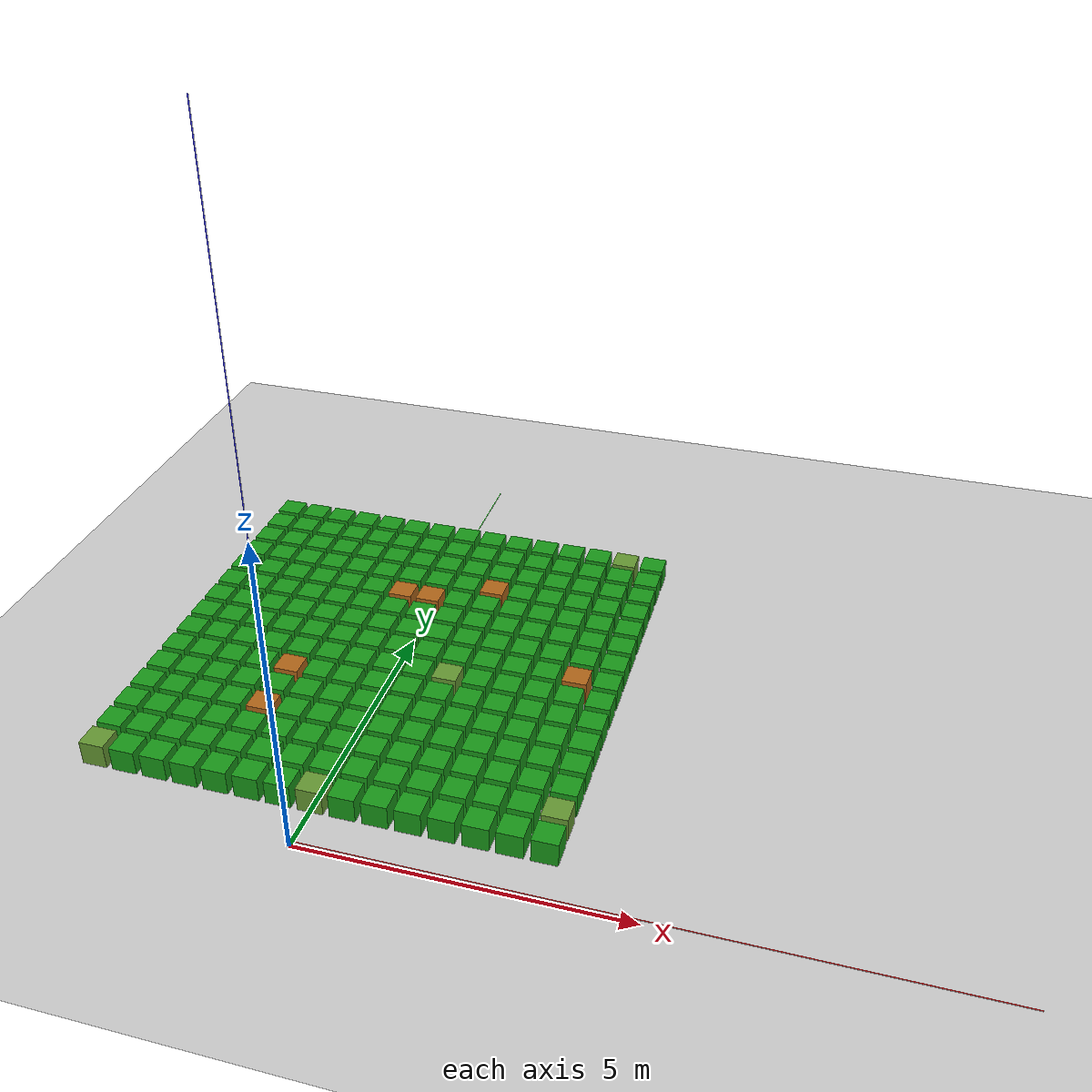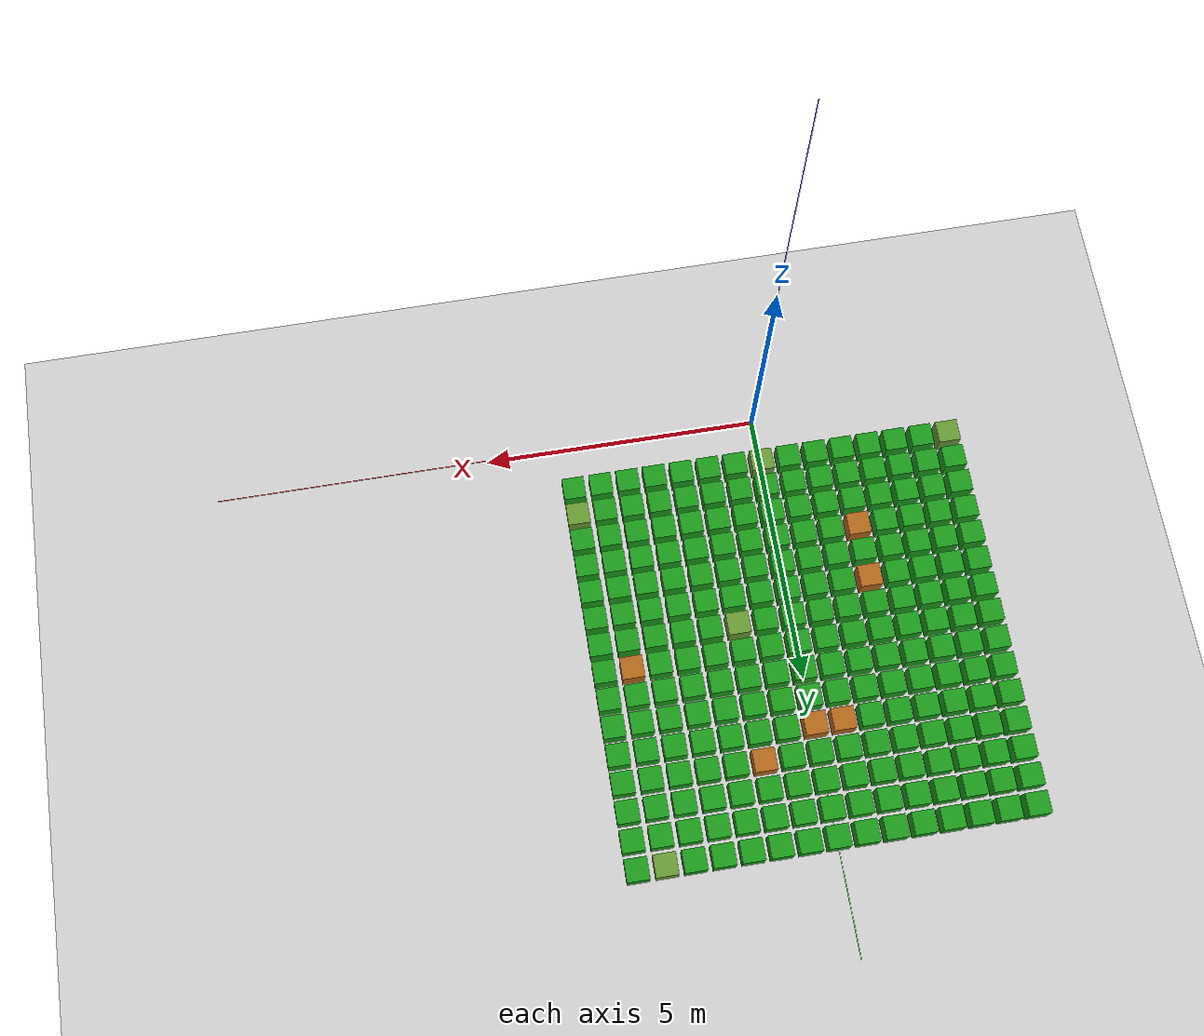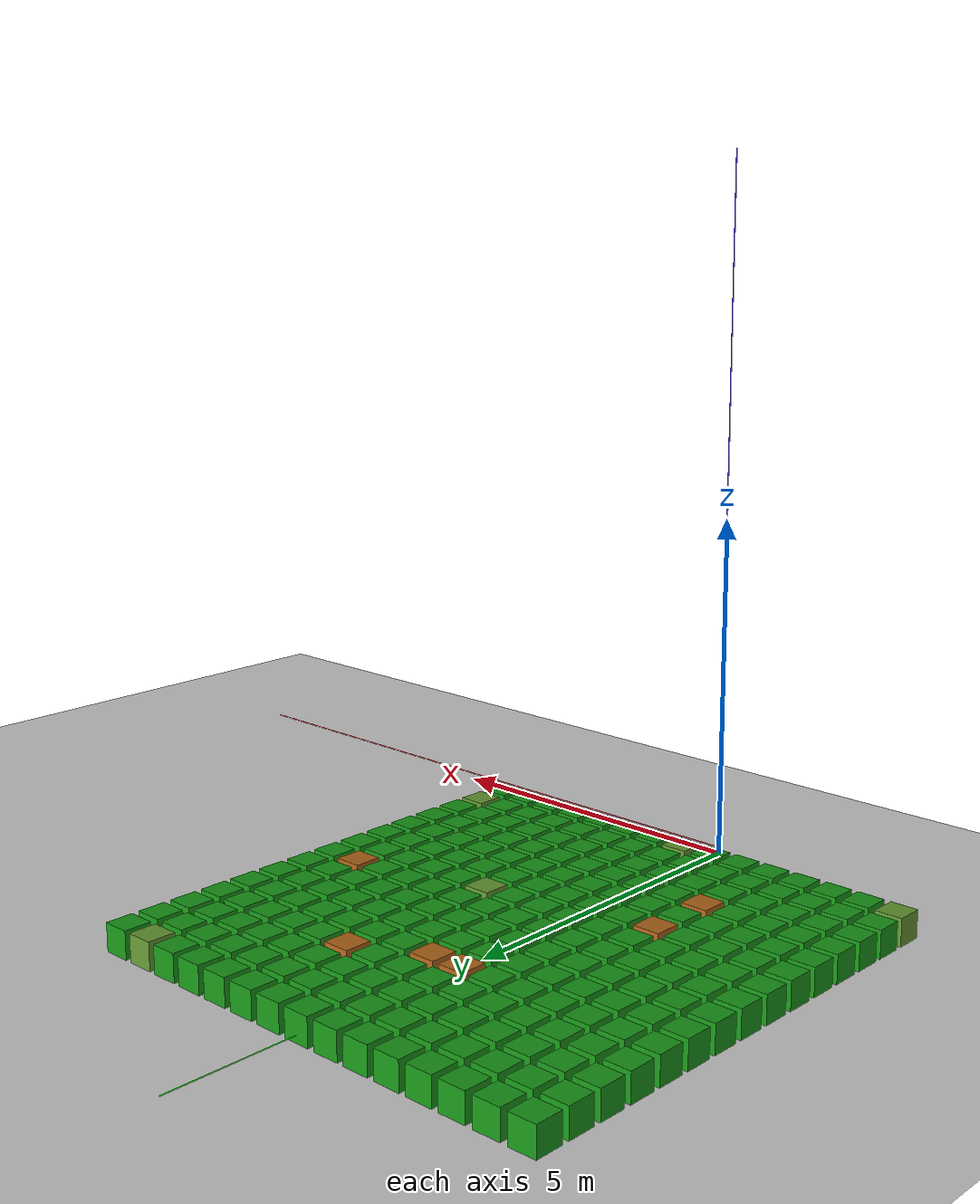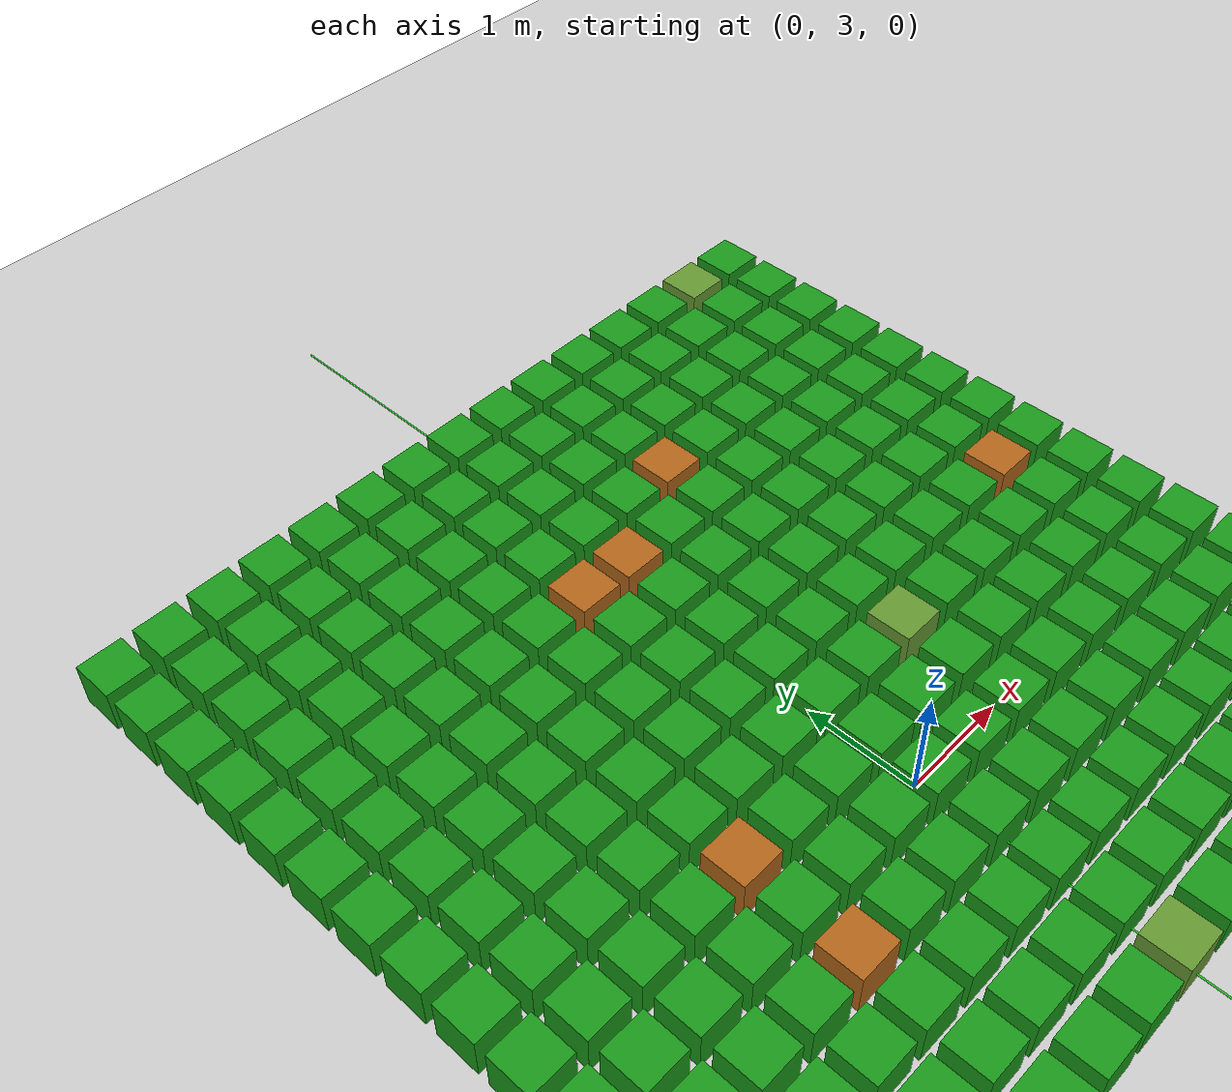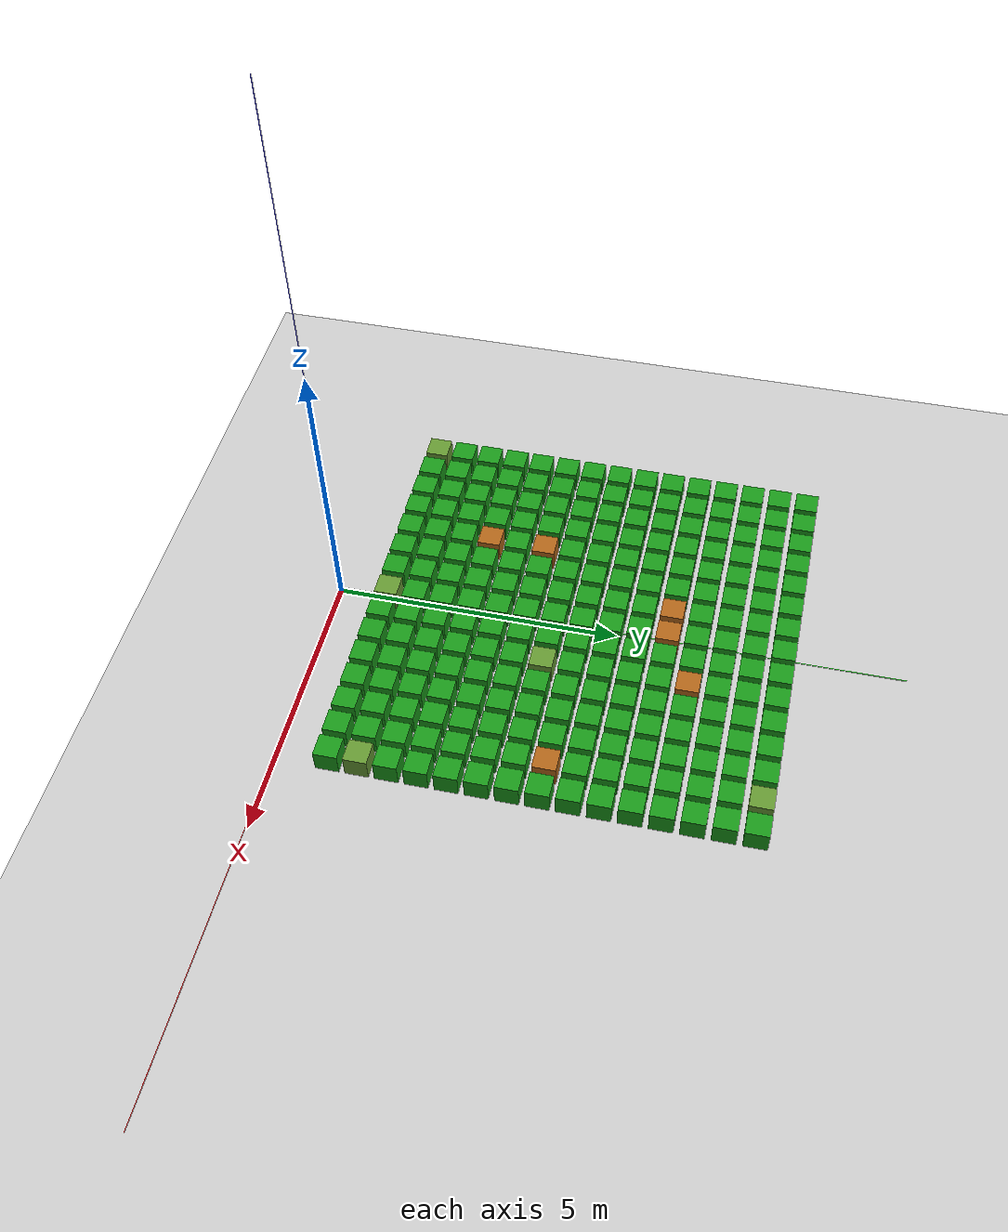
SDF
<sdf version="1.9">
 <world name="crop_detection">
  <physics name="fast_physics" type="ode">
   <max_step_size>0.001</max_step_size>
   <real_time_factor>1.0</real_time_factor>
  </physics>
  <plugin filename="gz-sim-physics-system" name="gz::sim::systems::Physics"/>
  <plugin filename="gz-sim-sensors-system" name="gz::sim::systems::Sensors">
   <render_engine>ogre2</render_engine>
  </plugin>
  <plugin filename="gz-sim-user-commands-system" name="gz::sim::systems::UserCommands"/>
  <plugin filename="gz-sim-scene-broadcaster-system" name="gz::sim::systems::SceneBroadcaster"/>
  <plugin filename="gz-sim-imu-system" name="gz::sim::systems::Imu"/>
  <plugin filename="gz-sim-navsat-system" name="gz::sim::systems::NavSat"/>
  <scene>
   <ambient>1.0 1.0 1.0</ambient>
   <background>0.7 0.9 1.0</background>
   <sky><clouds><speed>12</speed></clouds></sky>
   <shadows>1</shadows>
  </scene>
  <spherical_coordinates>
   <latitude_deg>-35.363261</latitude_deg>
   <longitude_deg>149.165230</longitude_deg>
   <elevation>584</elevation>
   <heading_deg>0</heading_deg>
   <surface_model>EARTH_WGS84</surface_model>
  </spherical_coordinates>
  <light type="directional" name="sun">
   <pose>0 0 100 0 0 0</pose>
   <diffuse>0.95 0.95 0.9 1</diffuse>
   <specular>0.5 0.5 0.5 1</specular>
   <attenuation>
    <range>1000</range>
    <constant>0.9</constant>
    <linear>0.01</linear>
    <quadratic>0.001</quadratic>
   </attenuation>
   <direction>-0.5 0.1 -0.9</direction>
  </light>
  <model name="axes">
   <static>1</static>
   <link name="link">
    <visual name="r">
     <cast_shadows>0</cast_shadows>
     <pose>5 0 0.1 0 0 0</pose>
     <geometry><box><size>10 0.01 0.01</size></box></geometry>
     <material>
      <ambient>1 0 0 0.8</ambient>
      <diffuse>1 0 0 0.8</diffuse>
      <emissive>1 0 0 0.8</emissive>
      <specular>0.5 0.5 0.5 0.8</specular>
     </material>
    </visual>
    <visual name="g">
     <cast_shadows>0</cast_shadows>
     <pose>0 5 0.1 0 0 0</pose>
     <geometry><box><size>0.01 10 0.01</size></box></geometry>
     <material>
      <ambient>0 1 0 0.8</ambient>
      <diffuse>0 1 0 0.8</diffuse>
      <emissive>0 1 0 0.8</emissive>
      <specular>0.5 0.5 0.5 0.8</specular>
     </material>
    </visual>
    <visual name="b">
     <cast_shadows>0</cast_shadows>
     <pose>0 0 5.1 0 0 0</pose>
     <geometry><box><size>0.01 0.01 10</size></box></geometry>
     <material>
      <ambient>0 0 1 0.8</ambient>
      <diffuse>0 0 1 0.8</diffuse>
      <emissive>0 0 1 0.8</emissive>
      <specular>0.5 0.5 0.5 0.8</specular>
     </material>
    </visual>
    <sensor name="navsat_sensor" type="navsat"><always_on>1</always_on><update_rate>1</update_rate></sensor>
   </link>
  </model>
  <model name="ground_plane">
   <static>true</static>
   <link name="link">
    <collision name="collision">
     <geometry><plane><normal>0 0 1</normal><size>100 100</size></plane></geometry>
    </collision>
    <visual name="visual">
     <geometry><plane><normal>0 0 1</normal><size>100 100</size></plane></geometry>
     <material><script><uri>model://ground_plane</uri><name>Gazebo/DryDirt</name></script></material>
    </visual>
   </link>
  </model>
  <model name="crop_1">
   <static>true</static>
   <link name="link">
    <visual name="visual">
     <geometry><box><size>0.4 0.4 0.4</size></box></geometry>
     <material><ambient>0.4 0.6 0.2 1</ambient><diffuse>0.4 0.6 0.2 1</diffuse></material>
    </visual>
    <pose>-3.500 0.900 0.200 0 0 0</pose>
   </link>
  </model>
  <model name="crop_2">
   <static>true</static>
   <link name="link">
    <visual name="visual">
     <geometry><box><size>0.4 0.4 0.4</size></box></geometry>
     <material><ambient>0.1 0.6 0.1 1</ambient><diffuse>0.1 0.6 0.1 1</diffuse></material>
    </visual>
    <pose>-3.000 0.900 0.200 0 0 0</pose>
   </link>
  </model>
  <model name="crop_3">
   <static>true</static>
   <link name="link">
    <visual name="visual">
     <geometry><box><size>0.4 0.4 0.4</size></box></geometry>
     <material><ambient>0.1 0.6 0.1 1</ambient><diffuse>0.1 0.6 0.1 1</diffuse></material>
    </visual>
    <pose>-2.500 0.900 0.200 0 0 0</pose>
   </link>
  </model>
  <model name="crop_4">
   <static>true</static>
   <link name="link">
    <visual name="visual">
     <geometry><box><size>0.4 0.4 0.4</size></box></geometry>
     <material><ambient>0.1 0.6 0.1 1</ambient><diffuse>0.1 0.6 0.1 1</diffuse></material>
    </visual>
    <pose>-2.000 0.900 0.200 0 0 0</pose>
   </link>
  </model>
  <model name="crop_5">
   <static>true</static>
   <link name="link">
    <visual name="visual">
     <geometry><box><size>0.4 0.4 0.4</size></box></geometry>
     <material><ambient>0.1 0.6 0.1 1</ambient><diffuse>0.1 0.6 0.1 1</diffuse></material>
    </visual>
    <pose>-1.500 0.900 0.200 0 0 0</pose>
   </link>
  </model>
  <model name="crop_6">
   <static>true</static>
   <link name="link">
    <visual name="visual">
     <geometry><box><size>0.4 0.4 0.4</size></box></geometry>
     <material><ambient>0.1 0.6 0.1 1</ambient><diffuse>0.1 0.6 0.1 1</diffuse></material>
    </visual>
    <pose>-1.000 0.900 0.200 0 0 0</pose>
   </link>
  </model>
  <model name="crop_7">
   <static>true</static>
   <link name="link">
    <visual name="visual">
     <geometry><box><size>0.4 0.4 0.4</size></box></geometry>
     <material><ambient>0.1 0.6 0.1 1</ambient><diffuse>0.1 0.6 0.1 1</diffuse></material>
    </visual>
    <pose>-0.500 0.900 0.200 0 0 0</pose>
   </link>
  </model>
  <model name="crop_8">
   <static>true</static>
   <link name="link">
    <visual name="visual">
     <geometry><box><size>0.4 0.4 0.4</size></box></geometry>
     <material><ambient>0.4 0.6 0.2 1</ambient><diffuse>0.4 0.6 0.2 1</diffuse></material>
    </visual>
    <pose>0.000 0.900 0.200 0 0 0</pose>
   </link>
  </model>
  <model name="crop_9">
   <static>true</static>
   <link name="link">
    <visual name="visual">
     <geometry><box><size>0.4 0.4 0.4</size></box></geometry>
     <material><ambient>0.1 0.6 0.1 1</ambient><diffuse>0.1 0.6 0.1 1</diffuse></material>
    </visual>
    <pose>0.500 0.900 0.200 0 0 0</pose>
   </link>
  </model>
  <model name="crop_10">
   <static>true</static>
   <link name="link">
    <visual name="visual">
     <geometry><box><size>0.4 0.4 0.4</size></box></geometry>
     <material><ambient>0.1 0.6 0.1 1</ambient><diffuse>0.1 0.6 0.1 1</diffuse></material>
    </visual>
    <pose>1.000 0.900 0.200 0 0 0</pose>
   </link>
  </model>
  <model name="crop_11">
   <static>true</static>
   <link name="link">
    <visual name="visual">
     <geometry><box><size>0.4 0.4 0.4</size></box></geometry>
     <material><ambient>0.1 0.6 0.1 1</ambient><diffuse>0.1 0.6 0.1 1</diffuse></material>
    </visual>
    <pose>1.500 0.900 0.200 0 0 0</pose>
   </link>
  </model>
  <model name="crop_12">
   <static>true</static>
   <link name="link">
    <visual name="visual">
     <geometry><box><size>0.4 0.4 0.4</size></box></geometry>
     <material><ambient>0.1 0.6 0.1 1</ambient><diffuse>0.1 0.6 0.1 1</diffuse></material>
    </visual>
    <pose>2.000 0.900 0.200 0 0 0</pose>
   </link>
  </model>
  <model name="crop_13">
   <static>true</static>
   <link name="link">
    <visual name="visual">
     <geometry><box><size>0.4 0.4 0.4</size></box></geometry>
     <material><ambient>0.1 0.6 0.1 1</ambient><diffuse>0.1 0.6 0.1 1</diffuse></material>
    </visual>
    <pose>2.500 0.900 0.200 0 0 0</pose>
   </link>
  </model>
  <model name="crop_14">
   <static>true</static>
   <link name="link">
    <visual name="visual">
     <geometry><box><size>0.4 0.4 0.4</size></box></geometry>
     <material><ambient>0.1 0.6 0.1 1</ambient><diffuse>0.1 0.6 0.1 1</diffuse></material>
    </visual>
    <pose>3.000 0.900 0.200 0 0 0</pose>
   </link>
  </model>
  <model name="crop_15">
   <static>true</static>
   <link name="link">
    <visual name="visual">
     <geometry><box><size>0.4 0.4 0.4</size></box></geometry>
     <material><ambient>0.1 0.6 0.1 1</ambient><diffuse>0.1 0.6 0.1 1</diffuse></material>
    </visual>
    <pose>3.500 0.900 0.200 0 0 0</pose>
   </link>
  </model>
  <model name="crop_16">
   <static>true</static>
   <link name="link">
    <visual name="visual">
     <geometry><box><size>0.4 0.4 0.4</size></box></geometry>
     <material><ambient>0.1 0.6 0.1 1</ambient><diffuse>0.1 0.6 0.1 1</diffuse></material>
    </visual>
    <pose>-3.500 1.400 0.200 0 0 0</pose>
   </link>
  </model>
  <model name="crop_17">
   <static>true</static>
   <link name="link">
    <visual name="visual">
     <geometry><box><size>0.4 0.4 0.4</size></box></geometry>
     <material><ambient>0.1 0.6 0.1 1</ambient><diffuse>0.1 0.6 0.1 1</diffuse></material>
    </visual>
    <pose>-3.000 1.400 0.200 0 0 0</pose>
   </link>
  </model>
  <model name="crop_18">
   <static>true</static>
   <link name="link">
    <visual name="visual">
     <geometry><box><size>0.4 0.4 0.4</size></box></geometry>
     <material><ambient>0.1 0.6 0.1 1</ambient><diffuse>0.1 0.6 0.1 1</diffuse></material>
    </visual>
    <pose>-2.500 1.400 0.200 0 0 0</pose>
   </link>
  </model>
  <model name="crop_19">
   <static>true</static>
   <link name="link">
    <visual name="visual">
     <geometry><box><size>0.4 0.4 0.4</size></box></geometry>
     <material><ambient>0.1 0.6 0.1 1</ambient><diffuse>0.1 0.6 0.1 1</diffuse></material>
    </visual>
    <pose>-2.000 1.400 0.200 0 0 0</pose>
   </link>
  </model>
  <model name="crop_20">
   <static>true</static>
   <link name="link">
    <visual name="visual">
     <geometry><box><size>0.4 0.4 0.4</size></box></geometry>
     <material><ambient>0.1 0.6 0.1 1</ambient><diffuse>0.1 0.6 0.1 1</diffuse></material>
    </visual>
    <pose>-1.500 1.400 0.200 0 0 0</pose>
   </link>
  </model>
  <model name="crop_21">
   <static>true</static>
   <link name="link">
    <visual name="visual">
     <geometry><box><size>0.4 0.4 0.4</size></box></geometry>
     <material><ambient>0.1 0.6 0.1 1</ambient><diffuse>0.1 0.6 0.1 1</diffuse></material>
    </visual>
    <pose>-1.000 1.400 0.200 0 0 0</pose>
   </link>
  </model>
  <model name="crop_22">
   <static>true</static>
   <link name="link">
    <visual name="visual">
     <geometry><box><size>0.4 0.4 0.4</size></box></geometry>
     <material><ambient>0.1 0.6 0.1 1</ambient><diffuse>0.1 0.6 0.1 1</diffuse></material>
    </visual>
    <pose>-0.500 1.400 0.200 0 0 0</pose>
   </link>
  </model>
  <model name="crop_23">
   <static>true</static>
   <link name="link">
    <visual name="visual">
     <geometry><box><size>0.4 0.4 0.4</size></box></geometry>
     <material><ambient>0.1 0.6 0.1 1</ambient><diffuse>0.1 0.6 0.1 1</diffuse></material>
    </visual>
    <pose>0.000 1.400 0.200 0 0 0</pose>
   </link>
  </model>
  <model name="crop_24">
   <static>true</static>
   <link name="link">
    <visual name="visual">
     <geometry><box><size>0.4 0.4 0.4</size></box></geometry>
     <material><ambient>0.1 0.6 0.1 1</ambient><diffuse>0.1 0.6 0.1 1</diffuse></material>
    </visual>
    <pose>0.500 1.400 0.200 0 0 0</pose>
   </link>
  </model>
  <model name="crop_25">
   <static>true</static>
   <link name="link">
    <visual name="visual">
     <geometry><box><size>0.4 0.4 0.4</size></box></geometry>
     <material><ambient>0.1 0.6 0.1 1</ambient><diffuse>0.1 0.6 0.1 1</diffuse></material>
    </visual>
    <pose>1.000 1.400 0.200 0 0 0</pose>
   </link>
  </model>
  <model name="crop_26">
   <static>true</static>
   <link name="link">
    <visual name="visual">
     <geometry><box><size>0.4 0.4 0.4</size></box></geometry>
     <material><ambient>0.1 0.6 0.1 1</ambient><diffuse>0.1 0.6 0.1 1</diffuse></material>
    </visual>
    <pose>1.500 1.400 0.200 0 0 0</pose>
   </link>
  </model>
  <model name="crop_27">
   <static>true</static>
   <link name="link">
    <visual name="visual">
     <geometry><box><size>0.4 0.4 0.4</size></box></geometry>
     <material><ambient>0.1 0.6 0.1 1</ambient><diffuse>0.1 0.6 0.1 1</diffuse></material>
    </visual>
    <pose>2.000 1.400 0.200 0 0 0</pose>
   </link>
  </model>
  <model name="crop_28">
   <static>true</static>
   <link name="link">
    <visual name="visual">
     <geometry><box><size>0.4 0.4 0.4</size></box></geometry>
     <material><ambient>0.1 0.6 0.1 1</ambient><diffuse>0.1 0.6 0.1 1</diffuse></material>
    </visual>
    <pose>2.500 1.400 0.200 0 0 0</pose>
   </link>
  </model>
  <model name="crop_29">
   <static>true</static>
   <link name="link">
    <visual name="visual">
     <geometry><box><size>0.4 0.4 0.4</size></box></geometry>
     <material><ambient>0.1 0.6 0.1 1</ambient><diffuse>0.1 0.6 0.1 1</diffuse></material>
    </visual>
    <pose>3.000 1.400 0.200 0 0 0</pose>
   </link>
  </model>
  <model name="crop_30">
   <static>true</static>
   <link name="link">
    <visual name="visual">
     <geometry><box><size>0.4 0.4 0.4</size></box></geometry>
     <material><ambient>0.4 0.6 0.2 1</ambient><diffuse>0.4 0.6 0.2 1</diffuse></material>
    </visual>
    <pose>3.500 1.400 0.200 0 0 0</pose>
   </link>
  </model>
  <model name="crop_31">
   <static>true</static>
   <link name="link">
    <visual name="visual">
     <geometry><box><size>0.4 0.4 0.4</size></box></geometry>
     <material><ambient>0.1 0.6 0.1 1</ambient><diffuse>0.1 0.6 0.1 1</diffuse></material>
    </visual>
    <pose>-3.500 1.900 0.200 0 0 0</pose>
   </link>
  </model>
  <model name="crop_32">
   <static>true</static>
   <link name="link">
    <visual name="visual">
     <geometry><box><size>0.4 0.4 0.4</size></box></geometry>
     <material><ambient>0.1 0.6 0.1 1</ambient><diffuse>0.1 0.6 0.1 1</diffuse></material>
    </visual>
    <pose>-3.000 1.900 0.200 0 0 0</pose>
   </link>
  </model>
  <model name="crop_33">
   <static>true</static>
   <link name="link">
    <visual name="visual">
     <geometry><box><size>0.4 0.4 0.4</size></box></geometry>
     <material><ambient>0.1 0.6 0.1 1</ambient><diffuse>0.1 0.6 0.1 1</diffuse></material>
    </visual>
    <pose>-2.500 1.900 0.200 0 0 0</pose>
   </link>
  </model>
  <model name="crop_34">
   <static>true</static>
   <link name="link">
    <visual name="visual">
     <geometry><box><size>0.4 0.4 0.4</size></box></geometry>
     <material><ambient>0.1 0.6 0.1 1</ambient><diffuse>0.1 0.6 0.1 1</diffuse></material>
    </visual>
    <pose>-2.000 1.900 0.200 0 0 0</pose>
   </link>
  </model>
  <model name="crop_35">
   <static>true</static>
   <link name="link">
    <visual name="visual">
     <geometry><box><size>0.4 0.4 0.4</size></box></geometry>
     <material><ambient>0.1 0.6 0.1 1</ambient><diffuse>0.1 0.6 0.1 1</diffuse></material>
    </visual>
    <pose>-1.500 1.900 0.200 0 0 0</pose>
   </link>
  </model>
  <model name="crop_36">
   <static>true</static>
   <link name="link">
    <visual name="visual">
     <geometry><box><size>0.4 0.4 0.4</size></box></geometry>
     <material><ambient>0.1 0.6 0.1 1</ambient><diffuse>0.1 0.6 0.1 1</diffuse></material>
    </visual>
    <pose>-1.000 1.900 0.200 0 0 0</pose>
   </link>
  </model>
  <model name="crop_37">
   <static>true</static>
   <link name="link">
    <visual name="visual">
     <geometry><box><size>0.4 0.4 0.4</size></box></geometry>
     <material><ambient>0.1 0.6 0.1 1</ambient><diffuse>0.1 0.6 0.1 1</diffuse></material>
    </visual>
    <pose>-0.500 1.900 0.200 0 0 0</pose>
   </link>
  </model>
  <model name="crop_38">
   <static>true</static>
   <link name="link">
    <visual name="visual">
     <geometry><box><size>0.4 0.4 0.4</size></box></geometry>
     <material><ambient>0.1 0.6 0.1 1</ambient><diffuse>0.1 0.6 0.1 1</diffuse></material>
    </visual>
    <pose>0.000 1.900 0.200 0 0 0</pose>
   </link>
  </model>
  <model name="crop_39">
   <static>true</static>
   <link name="link">
    <visual name="visual">
     <geometry><box><size>0.4 0.4 0.4</size></box></geometry>
     <material><ambient>0.1 0.6 0.1 1</ambient><diffuse>0.1 0.6 0.1 1</diffuse></material>
    </visual>
    <pose>0.500 1.900 0.200 0 0 0</pose>
   </link>
  </model>
  <model name="crop_40">
   <static>true</static>
   <link name="link">
    <visual name="visual">
     <geometry><box><size>0.4 0.4 0.4</size></box></geometry>
     <material><ambient>0.1 0.6 0.1 1</ambient><diffuse>0.1 0.6 0.1 1</diffuse></material>
    </visual>
    <pose>1.000 1.900 0.200 0 0 0</pose>
   </link>
  </model>
  <model name="crop_41">
   <static>true</static>
   <link name="link">
    <visual name="visual">
     <geometry><box><size>0.4 0.4 0.4</size></box></geometry>
     <material><ambient>0.1 0.6 0.1 1</ambient><diffuse>0.1 0.6 0.1 1</diffuse></material>
    </visual>
    <pose>1.500 1.900 0.200 0 0 0</pose>
   </link>
  </model>
  <model name="crop_42">
   <static>true</static>
   <link name="link">
    <visual name="visual">
     <geometry><box><size>0.4 0.4 0.4</size></box></geometry>
     <material><ambient>0.1 0.6 0.1 1</ambient><diffuse>0.1 0.6 0.1 1</diffuse></material>
    </visual>
    <pose>2.000 1.900 0.200 0 0 0</pose>
   </link>
  </model>
  <model name="crop_43">
   <static>true</static>
   <link name="link">
    <visual name="visual">
     <geometry><box><size>0.4 0.4 0.4</size></box></geometry>
     <material><ambient>0.1 0.6 0.1 1</ambient><diffuse>0.1 0.6 0.1 1</diffuse></material>
    </visual>
    <pose>2.500 1.900 0.200 0 0 0</pose>
   </link>
  </model>
  <model name="crop_44">
   <static>true</static>
   <link name="link">
    <visual name="visual">
     <geometry><box><size>0.4 0.4 0.4</size></box></geometry>
     <material><ambient>0.1 0.6 0.1 1</ambient><diffuse>0.1 0.6 0.1 1</diffuse></material>
    </visual>
    <pose>3.000 1.900 0.200 0 0 0</pose>
   </link>
  </model>
  <model name="crop_45">
   <static>true</static>
   <link name="link">
    <visual name="visual">
     <geometry><box><size>0.4 0.4 0.4</size></box></geometry>
     <material><ambient>0.1 0.6 0.1 1</ambient><diffuse>0.1 0.6 0.1 1</diffuse></material>
    </visual>
    <pose>3.500 1.900 0.200 0 0 0</pose>
   </link>
  </model>
  <model name="crop_46">
   <static>true</static>
   <link name="link">
    <visual name="visual">
     <geometry><box><size>0.4 0.4 0.4</size></box></geometry>
     <material><ambient>0.1 0.6 0.1 1</ambient><diffuse>0.1 0.6 0.1 1</diffuse></material>
    </visual>
    <pose>-3.500 2.400 0.200 0 0 0</pose>
   </link>
  </model>
  <model name="crop_47">
   <static>true</static>
   <link name="link">
    <visual name="visual">
     <geometry><box><size>0.4 0.4 0.4</size></box></geometry>
     <material><ambient>0.1 0.6 0.1 1</ambient><diffuse>0.1 0.6 0.1 1</diffuse></material>
    </visual>
    <pose>-3.000 2.400 0.200 0 0 0</pose>
   </link>
  </model>
  <model name="crop_48">
   <static>true</static>
   <link name="link">
    <visual name="visual">
     <geometry><box><size>0.4 0.4 0.4</size></box></geometry>
     <material><ambient>0.1 0.6 0.1 1</ambient><diffuse>0.1 0.6 0.1 1</diffuse></material>
    </visual>
    <pose>-2.500 2.400 0.200 0 0 0</pose>
   </link>
  </model>
  <model name="crop_49">
   <static>true</static>
   <link name="link">
    <visual name="visual">
     <geometry><box><size>0.4 0.4 0.4</size></box></geometry>
     <material><ambient>0.1 0.6 0.1 1</ambient><diffuse>0.1 0.6 0.1 1</diffuse></material>
    </visual>
    <pose>-2.000 2.400 0.200 0 0 0</pose>
   </link>
  </model>
  <model name="crop_50">
   <static>true</static>
   <link name="link">
    <visual name="visual">
     <geometry><box><size>0.4 0.4 0.4</size></box></geometry>
     <material><ambient>0.7 0.4 0.1 1</ambient><diffuse>0.7 0.4 0.1 1</diffuse></material>
    </visual>
    <pose>-1.500 2.400 0.200 0 0 0</pose>
   </link>
  </model>
  <model name="crop_51">
   <static>true</static>
   <link name="link">
    <visual name="visual">
     <geometry><box><size>0.4 0.4 0.4</size></box></geometry>
     <material><ambient>0.1 0.6 0.1 1</ambient><diffuse>0.1 0.6 0.1 1</diffuse></material>
    </visual>
    <pose>-1.000 2.400 0.200 0 0 0</pose>
   </link>
  </model>
  <model name="crop_52">
   <static>true</static>
   <link name="link">
    <visual name="visual">
     <geometry><box><size>0.4 0.4 0.4</size></box></geometry>
     <material><ambient>0.1 0.6 0.1 1</ambient><diffuse>0.1 0.6 0.1 1</diffuse></material>
    </visual>
    <pose>-0.500 2.400 0.200 0 0 0</pose>
   </link>
  </model>
  <model name="crop_53">
   <static>true</static>
   <link name="link">
    <visual name="visual">
     <geometry><box><size>0.4 0.4 0.4</size></box></geometry>
     <material><ambient>0.1 0.6 0.1 1</ambient><diffuse>0.1 0.6 0.1 1</diffuse></material>
    </visual>
    <pose>0.000 2.400 0.200 0 0 0</pose>
   </link>
  </model>
  <model name="crop_54">
   <static>true</static>
   <link name="link">
    <visual name="visual">
     <geometry><box><size>0.4 0.4 0.4</size></box></geometry>
     <material><ambient>0.1 0.6 0.1 1</ambient><diffuse>0.1 0.6 0.1 1</diffuse></material>
    </visual>
    <pose>0.500 2.400 0.200 0 0 0</pose>
   </link>
  </model>
  <model name="crop_55">
   <static>true</static>
   <link name="link">
    <visual name="visual">
     <geometry><box><size>0.4 0.4 0.4</size></box></geometry>
     <material><ambient>0.1 0.6 0.1 1</ambient><diffuse>0.1 0.6 0.1 1</diffuse></material>
    </visual>
    <pose>1.000 2.400 0.200 0 0 0</pose>
   </link>
  </model>
  <model name="crop_56">
   <static>true</static>
   <link name="link">
    <visual name="visual">
     <geometry><box><size>0.4 0.4 0.4</size></box></geometry>
     <material><ambient>0.1 0.6 0.1 1</ambient><diffuse>0.1 0.6 0.1 1</diffuse></material>
    </visual>
    <pose>1.500 2.400 0.200 0 0 0</pose>
   </link>
  </model>
  <model name="crop_57">
   <static>true</static>
   <link name="link">
    <visual name="visual">
     <geometry><box><size>0.4 0.4 0.4</size></box></geometry>
     <material><ambient>0.1 0.6 0.1 1</ambient><diffuse>0.1 0.6 0.1 1</diffuse></material>
    </visual>
    <pose>2.000 2.400 0.200 0 0 0</pose>
   </link>
  </model>
  <model name="crop_58">
   <static>true</static>
   <link name="link">
    <visual name="visual">
     <geometry><box><size>0.4 0.4 0.4</size></box></geometry>
     <material><ambient>0.1 0.6 0.1 1</ambient><diffuse>0.1 0.6 0.1 1</diffuse></material>
    </visual>
    <pose>2.500 2.400 0.200 0 0 0</pose>
   </link>
  </model>
  <model name="crop_59">
   <static>true</static>
   <link name="link">
    <visual name="visual">
     <geometry><box><size>0.4 0.4 0.4</size></box></geometry>
     <material><ambient>0.1 0.6 0.1 1</ambient><diffuse>0.1 0.6 0.1 1</diffuse></material>
    </visual>
    <pose>3.000 2.400 0.200 0 0 0</pose>
   </link>
  </model>
  <model name="crop_60">
   <static>true</static>
   <link name="link">
    <visual name="visual">
     <geometry><box><size>0.4 0.4 0.4</size></box></geometry>
     <material><ambient>0.1 0.6 0.1 1</ambient><diffuse>0.1 0.6 0.1 1</diffuse></material>
    </visual>
    <pose>3.500 2.400 0.200 0 0 0</pose>
   </link>
  </model>
  <model name="crop_61">
   <static>true</static>
   <link name="link">
    <visual name="visual">
     <geometry><box><size>0.4 0.4 0.4</size></box></geometry>
     <material><ambient>0.1 0.6 0.1 1</ambient><diffuse>0.1 0.6 0.1 1</diffuse></material>
    </visual>
    <pose>-3.500 2.900 0.200 0 0 0</pose>
   </link>
  </model>
  <model name="crop_62">
   <static>true</static>
   <link name="link">
    <visual name="visual">
     <geometry><box><size>0.4 0.4 0.4</size></box></geometry>
     <material><ambient>0.1 0.6 0.1 1</ambient><diffuse>0.1 0.6 0.1 1</diffuse></material>
    </visual>
    <pose>-3.000 2.900 0.200 0 0 0</pose>
   </link>
  </model>
  <model name="crop_63">
   <static>true</static>
   <link name="link">
    <visual name="visual">
     <geometry><box><size>0.4 0.4 0.4</size></box></geometry>
     <material><ambient>0.1 0.6 0.1 1</ambient><diffuse>0.1 0.6 0.1 1</diffuse></material>
    </visual>
    <pose>-2.500 2.900 0.200 0 0 0</pose>
   </link>
  </model>
  <model name="crop_64">
   <static>true</static>
   <link name="link">
    <visual name="visual">
     <geometry><box><size>0.4 0.4 0.4</size></box></geometry>
     <material><ambient>0.1 0.6 0.1 1</ambient><diffuse>0.1 0.6 0.1 1</diffuse></material>
    </visual>
    <pose>-2.000 2.900 0.200 0 0 0</pose>
   </link>
  </model>
  <model name="crop_65">
   <static>true</static>
   <link name="link">
    <visual name="visual">
     <geometry><box><size>0.4 0.4 0.4</size></box></geometry>
     <material><ambient>0.1 0.6 0.1 1</ambient><diffuse>0.1 0.6 0.1 1</diffuse></material>
    </visual>
    <pose>-1.500 2.900 0.200 0 0 0</pose>
   </link>
  </model>
  <model name="crop_66">
   <static>true</static>
   <link name="link">
    <visual name="visual">
     <geometry><box><size>0.4 0.4 0.4</size></box></geometry>
     <material><ambient>0.1 0.6 0.1 1</ambient><diffuse>0.1 0.6 0.1 1</diffuse></material>
    </visual>
    <pose>-1.000 2.900 0.200 0 0 0</pose>
   </link>
  </model>
  <model name="crop_67">
   <static>true</static>
   <link name="link">
    <visual name="visual">
     <geometry><box><size>0.4 0.4 0.4</size></box></geometry>
     <material><ambient>0.1 0.6 0.1 1</ambient><diffuse>0.1 0.6 0.1 1</diffuse></material>
    </visual>
    <pose>-0.500 2.900 0.200 0 0 0</pose>
   </link>
  </model>
  <model name="crop_68">
   <static>true</static>
   <link name="link">
    <visual name="visual">
     <geometry><box><size>0.4 0.4 0.4</size></box></geometry>
     <material><ambient>0.1 0.6 0.1 1</ambient><diffuse>0.1 0.6 0.1 1</diffuse></material>
    </visual>
    <pose>0.000 2.900 0.200 0 0 0</pose>
   </link>
  </model>
  <model name="crop_69">
   <static>true</static>
   <link name="link">
    <visual name="visual">
     <geometry><box><size>0.4 0.4 0.4</size></box></geometry>
     <material><ambient>0.1 0.6 0.1 1</ambient><diffuse>0.1 0.6 0.1 1</diffuse></material>
    </visual>
    <pose>0.500 2.900 0.200 0 0 0</pose>
   </link>
  </model>
  <model name="crop_70">
   <static>true</static>
   <link name="link">
    <visual name="visual">
     <geometry><box><size>0.4 0.4 0.4</size></box></geometry>
     <material><ambient>0.1 0.6 0.1 1</ambient><diffuse>0.1 0.6 0.1 1</diffuse></material>
    </visual>
    <pose>1.000 2.900 0.200 0 0 0</pose>
   </link>
  </model>
  <model name="crop_71">
   <static>true</static>
   <link name="link">
    <visual name="visual">
     <geometry><box><size>0.4 0.4 0.4</size></box></geometry>
     <material><ambient>0.1 0.6 0.1 1</ambient><diffuse>0.1 0.6 0.1 1</diffuse></material>
    </visual>
    <pose>1.500 2.900 0.200 0 0 0</pose>
   </link>
  </model>
  <model name="crop_72">
   <static>true</static>
   <link name="link">
    <visual name="visual">
     <geometry><box><size>0.4 0.4 0.4</size></box></geometry>
     <material><ambient>0.1 0.6 0.1 1</ambient><diffuse>0.1 0.6 0.1 1</diffuse></material>
    </visual>
    <pose>2.000 2.900 0.200 0 0 0</pose>
   </link>
  </model>
  <model name="crop_73">
   <static>true</static>
   <link name="link">
    <visual name="visual">
     <geometry><box><size>0.4 0.4 0.4</size></box></geometry>
     <material><ambient>0.1 0.6 0.1 1</ambient><diffuse>0.1 0.6 0.1 1</diffuse></material>
    </visual>
    <pose>2.500 2.900 0.200 0 0 0</pose>
   </link>
  </model>
  <model name="crop_74">
   <static>true</static>
   <link name="link">
    <visual name="visual">
     <geometry><box><size>0.4 0.4 0.4</size></box></geometry>
     <material><ambient>0.1 0.6 0.1 1</ambient><diffuse>0.1 0.6 0.1 1</diffuse></material>
    </visual>
    <pose>3.000 2.900 0.200 0 0 0</pose>
   </link>
  </model>
  <model name="crop_75">
   <static>true</static>
   <link name="link">
    <visual name="visual">
     <geometry><box><size>0.4 0.4 0.4</size></box></geometry>
     <material><ambient>0.1 0.6 0.1 1</ambient><diffuse>0.1 0.6 0.1 1</diffuse></material>
    </visual>
    <pose>3.500 2.900 0.200 0 0 0</pose>
   </link>
  </model>
  <model name="crop_76">
   <static>true</static>
   <link name="link">
    <visual name="visual">
     <geometry><box><size>0.4 0.4 0.4</size></box></geometry>
     <material><ambient>0.1 0.6 0.1 1</ambient><diffuse>0.1 0.6 0.1 1</diffuse></material>
    </visual>
    <pose>-3.500 3.400 0.200 0 0 0</pose>
   </link>
  </model>
  <model name="crop_77">
   <static>true</static>
   <link name="link">
    <visual name="visual">
     <geometry><box><size>0.4 0.4 0.4</size></box></geometry>
     <material><ambient>0.1 0.6 0.1 1</ambient><diffuse>0.1 0.6 0.1 1</diffuse></material>
    </visual>
    <pose>-3.000 3.400 0.200 0 0 0</pose>
   </link>
  </model>
  <model name="crop_78">
   <static>true</static>
   <link name="link">
    <visual name="visual">
     <geometry><box><size>0.4 0.4 0.4</size></box></geometry>
     <material><ambient>0.1 0.6 0.1 1</ambient><diffuse>0.1 0.6 0.1 1</diffuse></material>
    </visual>
    <pose>-2.500 3.400 0.200 0 0 0</pose>
   </link>
  </model>
  <model name="crop_79">
   <static>true</static>
   <link name="link">
    <visual name="visual">
     <geometry><box><size>0.4 0.4 0.4</size></box></geometry>
     <material><ambient>0.1 0.6 0.1 1</ambient><diffuse>0.1 0.6 0.1 1</diffuse></material>
    </visual>
    <pose>-2.000 3.400 0.200 0 0 0</pose>
   </link>
  </model>
  <model name="crop_80">
   <static>true</static>
   <link name="link">
    <visual name="visual">
     <geometry><box><size>0.4 0.4 0.4</size></box></geometry>
     <material><ambient>0.7 0.4 0.1 1</ambient><diffuse>0.7 0.4 0.1 1</diffuse></material>
    </visual>
    <pose>-1.500 3.400 0.200 0 0 0</pose>
   </link>
  </model>
  <model name="crop_81">
   <static>true</static>
   <link name="link">
    <visual name="visual">
     <geometry><box><size>0.4 0.4 0.4</size></box></geometry>
     <material><ambient>0.1 0.6 0.1 1</ambient><diffuse>0.1 0.6 0.1 1</diffuse></material>
    </visual>
    <pose>-1.000 3.400 0.200 0 0 0</pose>
   </link>
  </model>
  <model name="crop_82">
   <static>true</static>
   <link name="link">
    <visual name="visual">
     <geometry><box><size>0.4 0.4 0.4</size></box></geometry>
     <material><ambient>0.1 0.6 0.1 1</ambient><diffuse>0.1 0.6 0.1 1</diffuse></material>
    </visual>
    <pose>-0.500 3.400 0.200 0 0 0</pose>
   </link>
  </model>
  <model name="crop_83">
   <static>true</static>
   <link name="link">
    <visual name="visual">
     <geometry><box><size>0.4 0.4 0.4</size></box></geometry>
     <material><ambient>0.1 0.6 0.1 1</ambient><diffuse>0.1 0.6 0.1 1</diffuse></material>
    </visual>
    <pose>0.000 3.400 0.200 0 0 0</pose>
   </link>
  </model>
  <model name="crop_84">
   <static>true</static>
   <link name="link">
    <visual name="visual">
     <geometry><box><size>0.4 0.4 0.4</size></box></geometry>
     <material><ambient>0.1 0.6 0.1 1</ambient><diffuse>0.1 0.6 0.1 1</diffuse></material>
    </visual>
    <pose>0.500 3.400 0.200 0 0 0</pose>
   </link>
  </model>
  <model name="crop_85">
   <static>true</static>
   <link name="link">
    <visual name="visual">
     <geometry><box><size>0.4 0.4 0.4</size></box></geometry>
     <material><ambient>0.1 0.6 0.1 1</ambient><diffuse>0.1 0.6 0.1 1</diffuse></material>
    </visual>
    <pose>1.000 3.400 0.200 0 0 0</pose>
   </link>
  </model>
  <model name="crop_86">
   <static>true</static>
   <link name="link">
    <visual name="visual">
     <geometry><box><size>0.4 0.4 0.4</size></box></geometry>
     <material><ambient>0.1 0.6 0.1 1</ambient><diffuse>0.1 0.6 0.1 1</diffuse></material>
    </visual>
    <pose>1.500 3.400 0.200 0 0 0</pose>
   </link>
  </model>
  <model name="crop_87">
   <static>true</static>
   <link name="link">
    <visual name="visual">
     <geometry><box><size>0.4 0.4 0.4</size></box></geometry>
     <material><ambient>0.1 0.6 0.1 1</ambient><diffuse>0.1 0.6 0.1 1</diffuse></material>
    </visual>
    <pose>2.000 3.400 0.200 0 0 0</pose>
   </link>
  </model>
  <model name="crop_88">
   <static>true</static>
   <link name="link">
    <visual name="visual">
     <geometry><box><size>0.4 0.4 0.4</size></box></geometry>
     <material><ambient>0.1 0.6 0.1 1</ambient><diffuse>0.1 0.6 0.1 1</diffuse></material>
    </visual>
    <pose>2.500 3.400 0.200 0 0 0</pose>
   </link>
  </model>
  <model name="crop_89">
   <static>true</static>
   <link name="link">
    <visual name="visual">
     <geometry><box><size>0.4 0.4 0.4</size></box></geometry>
     <material><ambient>0.1 0.6 0.1 1</ambient><diffuse>0.1 0.6 0.1 1</diffuse></material>
    </visual>
    <pose>3.000 3.400 0.200 0 0 0</pose>
   </link>
  </model>
  <model name="crop_90">
   <static>true</static>
   <link name="link">
    <visual name="visual">
     <geometry><box><size>0.4 0.4 0.4</size></box></geometry>
     <material><ambient>0.1 0.6 0.1 1</ambient><diffuse>0.1 0.6 0.1 1</diffuse></material>
    </visual>
    <pose>3.500 3.400 0.200 0 0 0</pose>
   </link>
  </model>
  <model name="crop_91">
   <static>true</static>
   <link name="link">
    <visual name="visual">
     <geometry><box><size>0.4 0.4 0.4</size></box></geometry>
     <material><ambient>0.1 0.6 0.1 1</ambient><diffuse>0.1 0.6 0.1 1</diffuse></material>
    </visual>
    <pose>-3.500 3.900 0.200 0 0 0</pose>
   </link>
  </model>
  <model name="crop_92">
   <static>true</static>
   <link name="link">
    <visual name="visual">
     <geometry><box><size>0.4 0.4 0.4</size></box></geometry>
     <material><ambient>0.1 0.6 0.1 1</ambient><diffuse>0.1 0.6 0.1 1</diffuse></material>
    </visual>
    <pose>-3.000 3.900 0.200 0 0 0</pose>
   </link>
  </model>
  <model name="crop_93">
   <static>true</static>
   <link name="link">
    <visual name="visual">
     <geometry><box><size>0.4 0.4 0.4</size></box></geometry>
     <material><ambient>0.1 0.6 0.1 1</ambient><diffuse>0.1 0.6 0.1 1</diffuse></material>
    </visual>
    <pose>-2.500 3.900 0.200 0 0 0</pose>
   </link>
  </model>
  <model name="crop_94">
   <static>true</static>
   <link name="link">
    <visual name="visual">
     <geometry><box><size>0.4 0.4 0.4</size></box></geometry>
     <material><ambient>0.1 0.6 0.1 1</ambient><diffuse>0.1 0.6 0.1 1</diffuse></material>
    </visual>
    <pose>-2.000 3.900 0.200 0 0 0</pose>
   </link>
  </model>
  <model name="crop_95">
   <static>true</static>
   <link name="link">
    <visual name="visual">
     <geometry><box><size>0.4 0.4 0.4</size></box></geometry>
     <material><ambient>0.1 0.6 0.1 1</ambient><diffuse>0.1 0.6 0.1 1</diffuse></material>
    </visual>
    <pose>-1.500 3.900 0.200 0 0 0</pose>
   </link>
  </model>
  <model name="crop_96">
   <static>true</static>
   <link name="link">
    <visual name="visual">
     <geometry><box><size>0.4 0.4 0.4</size></box></geometry>
     <material><ambient>0.1 0.6 0.1 1</ambient><diffuse>0.1 0.6 0.1 1</diffuse></material>
    </visual>
    <pose>-1.000 3.900 0.200 0 0 0</pose>
   </link>
  </model>
  <model name="crop_97">
   <static>true</static>
   <link name="link">
    <visual name="visual">
     <geometry><box><size>0.4 0.4 0.4</size></box></geometry>
     <material><ambient>0.1 0.6 0.1 1</ambient><diffuse>0.1 0.6 0.1 1</diffuse></material>
    </visual>
    <pose>-0.500 3.900 0.200 0 0 0</pose>
   </link>
  </model>
  <model name="crop_98">
   <static>true</static>
   <link name="link">
    <visual name="visual">
     <geometry><box><size>0.4 0.4 0.4</size></box></geometry>
     <material><ambient>0.1 0.6 0.1 1</ambient><diffuse>0.1 0.6 0.1 1</diffuse></material>
    </visual>
    <pose>0.000 3.900 0.200 0 0 0</pose>
   </link>
  </model>
  <model name="crop_99">
   <static>true</static>
   <link name="link">
    <visual name="visual">
     <geometry><box><size>0.4 0.4 0.4</size></box></geometry>
     <material><ambient>0.1 0.6 0.1 1</ambient><diffuse>0.1 0.6 0.1 1</diffuse></material>
    </visual>
    <pose>0.500 3.900 0.200 0 0 0</pose>
   </link>
  </model>
  <model name="crop_100">
   <static>true</static>
   <link name="link">
    <visual name="visual">
     <geometry><box><size>0.4 0.4 0.4</size></box></geometry>
     <material><ambient>0.4 0.6 0.2 1</ambient><diffuse>0.4 0.6 0.2 1</diffuse></material>
    </visual>
    <pose>1.000 3.900 0.200 0 0 0</pose>
   </link>
  </model>
  <model name="crop_101">
   <static>true</static>
   <link name="link">
    <visual name="visual">
     <geometry><box><size>0.4 0.4 0.4</size></box></geometry>
     <material><ambient>0.1 0.6 0.1 1</ambient><diffuse>0.1 0.6 0.1 1</diffuse></material>
    </visual>
    <pose>1.500 3.900 0.200 0 0 0</pose>
   </link>
  </model>
  <model name="crop_102">
   <static>true</static>
   <link name="link">
    <visual name="visual">
     <geometry><box><size>0.4 0.4 0.4</size></box></geometry>
     <material><ambient>0.1 0.6 0.1 1</ambient><diffuse>0.1 0.6 0.1 1</diffuse></material>
    </visual>
    <pose>2.000 3.900 0.200 0 0 0</pose>
   </link>
  </model>
  <model name="crop_103">
   <static>true</static>
   <link name="link">
    <visual name="visual">
     <geometry><box><size>0.4 0.4 0.4</size></box></geometry>
     <material><ambient>0.1 0.6 0.1 1</ambient><diffuse>0.1 0.6 0.1 1</diffuse></material>
    </visual>
    <pose>2.500 3.900 0.200 0 0 0</pose>
   </link>
  </model>
  <model name="crop_104">
   <static>true</static>
   <link name="link">
    <visual name="visual">
     <geometry><box><size>0.4 0.4 0.4</size></box></geometry>
     <material><ambient>0.1 0.6 0.1 1</ambient><diffuse>0.1 0.6 0.1 1</diffuse></material>
    </visual>
    <pose>3.000 3.900 0.200 0 0 0</pose>
   </link>
  </model>
  <model name="crop_105">
   <static>true</static>
   <link name="link">
    <visual name="visual">
     <geometry><box><size>0.4 0.4 0.4</size></box></geometry>
     <material><ambient>0.1 0.6 0.1 1</ambient><diffuse>0.1 0.6 0.1 1</diffuse></material>
    </visual>
    <pose>3.500 3.900 0.200 0 0 0</pose>
   </link>
  </model>
  <model name="crop_106">
   <static>true</static>
   <link name="link">
    <visual name="visual">
     <geometry><box><size>0.4 0.4 0.4</size></box></geometry>
     <material><ambient>0.1 0.6 0.1 1</ambient><diffuse>0.1 0.6 0.1 1</diffuse></material>
    </visual>
    <pose>-3.500 4.400 0.200 0 0 0</pose>
   </link>
  </model>
  <model name="crop_107">
   <static>true</static>
   <link name="link">
    <visual name="visual">
     <geometry><box><size>0.4 0.4 0.4</size></box></geometry>
     <material><ambient>0.1 0.6 0.1 1</ambient><diffuse>0.1 0.6 0.1 1</diffuse></material>
    </visual>
    <pose>-3.000 4.400 0.200 0 0 0</pose>
   </link>
  </model>
  <model name="crop_108">
   <static>true</static>
   <link name="link">
    <visual name="visual">
     <geometry><box><size>0.4 0.4 0.4</size></box></geometry>
     <material><ambient>0.1 0.6 0.1 1</ambient><diffuse>0.1 0.6 0.1 1</diffuse></material>
    </visual>
    <pose>-2.500 4.400 0.200 0 0 0</pose>
   </link>
  </model>
  <model name="crop_109">
   <static>true</static>
   <link name="link">
    <visual name="visual">
     <geometry><box><size>0.4 0.4 0.4</size></box></geometry>
     <material><ambient>0.1 0.6 0.1 1</ambient><diffuse>0.1 0.6 0.1 1</diffuse></material>
    </visual>
    <pose>-2.000 4.400 0.200 0 0 0</pose>
   </link>
  </model>
  <model name="crop_110">
   <static>true</static>
   <link name="link">
    <visual name="visual">
     <geometry><box><size>0.4 0.4 0.4</size></box></geometry>
     <material><ambient>0.1 0.6 0.1 1</ambient><diffuse>0.1 0.6 0.1 1</diffuse></material>
    </visual>
    <pose>-1.500 4.400 0.200 0 0 0</pose>
   </link>
  </model>
  <model name="crop_111">
   <static>true</static>
   <link name="link">
    <visual name="visual">
     <geometry><box><size>0.4 0.4 0.4</size></box></geometry>
     <material><ambient>0.1 0.6 0.1 1</ambient><diffuse>0.1 0.6 0.1 1</diffuse></material>
    </visual>
    <pose>-1.000 4.400 0.200 0 0 0</pose>
   </link>
  </model>
  <model name="crop_112">
   <static>true</static>
   <link name="link">
    <visual name="visual">
     <geometry><box><size>0.4 0.4 0.4</size></box></geometry>
     <material><ambient>0.1 0.6 0.1 1</ambient><diffuse>0.1 0.6 0.1 1</diffuse></material>
    </visual>
    <pose>-0.500 4.400 0.200 0 0 0</pose>
   </link>
  </model>
  <model name="crop_113">
   <static>true</static>
   <link name="link">
    <visual name="visual">
     <geometry><box><size>0.4 0.4 0.4</size></box></geometry>
     <material><ambient>0.1 0.6 0.1 1</ambient><diffuse>0.1 0.6 0.1 1</diffuse></material>
    </visual>
    <pose>0.000 4.400 0.200 0 0 0</pose>
   </link>
  </model>
  <model name="crop_114">
   <static>true</static>
   <link name="link">
    <visual name="visual">
     <geometry><box><size>0.4 0.4 0.4</size></box></geometry>
     <material><ambient>0.1 0.6 0.1 1</ambient><diffuse>0.1 0.6 0.1 1</diffuse></material>
    </visual>
    <pose>0.500 4.400 0.200 0 0 0</pose>
   </link>
  </model>
  <model name="crop_115">
   <static>true</static>
   <link name="link">
    <visual name="visual">
     <geometry><box><size>0.4 0.4 0.4</size></box></geometry>
     <material><ambient>0.1 0.6 0.1 1</ambient><diffuse>0.1 0.6 0.1 1</diffuse></material>
    </visual>
    <pose>1.000 4.400 0.200 0 0 0</pose>
   </link>
  </model>
  <model name="crop_116">
   <static>true</static>
   <link name="link">
    <visual name="visual">
     <geometry><box><size>0.4 0.4 0.4</size></box></geometry>
     <material><ambient>0.1 0.6 0.1 1</ambient><diffuse>0.1 0.6 0.1 1</diffuse></material>
    </visual>
    <pose>1.500 4.400 0.200 0 0 0</pose>
   </link>
  </model>
  <model name="crop_117">
   <static>true</static>
   <link name="link">
    <visual name="visual">
     <geometry><box><size>0.4 0.4 0.4</size></box></geometry>
     <material><ambient>0.1 0.6 0.1 1</ambient><diffuse>0.1 0.6 0.1 1</diffuse></material>
    </visual>
    <pose>2.000 4.400 0.200 0 0 0</pose>
   </link>
  </model>
  <model name="crop_118">
   <static>true</static>
   <link name="link">
    <visual name="visual">
     <geometry><box><size>0.4 0.4 0.4</size></box></geometry>
     <material><ambient>0.1 0.6 0.1 1</ambient><diffuse>0.1 0.6 0.1 1</diffuse></material>
    </visual>
    <pose>2.500 4.400 0.200 0 0 0</pose>
   </link>
  </model>
  <model name="crop_119">
   <static>true</static>
   <link name="link">
    <visual name="visual">
     <geometry><box><size>0.4 0.4 0.4</size></box></geometry>
     <material><ambient>0.7 0.4 0.1 1</ambient><diffuse>0.7 0.4 0.1 1</diffuse></material>
    </visual>
    <pose>3.000 4.400 0.200 0 0 0</pose>
   </link>
  </model>
  <model name="crop_120">
   <static>true</static>
   <link name="link">
    <visual name="visual">
     <geometry><box><size>0.4 0.4 0.4</size></box></geometry>
     <material><ambient>0.1 0.6 0.1 1</ambient><diffuse>0.1 0.6 0.1 1</diffuse></material>
    </visual>
    <pose>3.500 4.400 0.200 0 0 0</pose>
   </link>
  </model>
  <model name="crop_121">
   <static>true</static>
   <link name="link">
    <visual name="visual">
     <geometry><box><size>0.4 0.4 0.4</size></box></geometry>
     <material><ambient>0.1 0.6 0.1 1</ambient><diffuse>0.1 0.6 0.1 1</diffuse></material>
    </visual>
    <pose>-3.500 4.900 0.200 0 0 0</pose>
   </link>
  </model>
  <model name="crop_122">
   <static>true</static>
   <link name="link">
    <visual name="visual">
     <geometry><box><size>0.4 0.4 0.4</size></box></geometry>
     <material><ambient>0.1 0.6 0.1 1</ambient><diffuse>0.1 0.6 0.1 1</diffuse></material>
    </visual>
    <pose>-3.000 4.900 0.200 0 0 0</pose>
   </link>
  </model>
  <model name="crop_123">
   <static>true</static>
   <link name="link">
    <visual name="visual">
     <geometry><box><size>0.4 0.4 0.4</size></box></geometry>
     <material><ambient>0.1 0.6 0.1 1</ambient><diffuse>0.1 0.6 0.1 1</diffuse></material>
    </visual>
    <pose>-2.500 4.900 0.200 0 0 0</pose>
   </link>
  </model>
  <model name="crop_124">
   <static>true</static>
   <link name="link">
    <visual name="visual">
     <geometry><box><size>0.4 0.4 0.4</size></box></geometry>
     <material><ambient>0.1 0.6 0.1 1</ambient><diffuse>0.1 0.6 0.1 1</diffuse></material>
    </visual>
    <pose>-2.000 4.900 0.200 0 0 0</pose>
   </link>
  </model>
  <model name="crop_125">
   <static>true</static>
   <link name="link">
    <visual name="visual">
     <geometry><box><size>0.4 0.4 0.4</size></box></geometry>
     <material><ambient>0.1 0.6 0.1 1</ambient><diffuse>0.1 0.6 0.1 1</diffuse></material>
    </visual>
    <pose>-1.500 4.900 0.200 0 0 0</pose>
   </link>
  </model>
  <model name="crop_126">
   <static>true</static>
   <link name="link">
    <visual name="visual">
     <geometry><box><size>0.4 0.4 0.4</size></box></geometry>
     <material><ambient>0.1 0.6 0.1 1</ambient><diffuse>0.1 0.6 0.1 1</diffuse></material>
    </visual>
    <pose>-1.000 4.900 0.200 0 0 0</pose>
   </link>
  </model>
  <model name="crop_127">
   <static>true</static>
   <link name="link">
    <visual name="visual">
     <geometry><box><size>0.4 0.4 0.4</size></box></geometry>
     <material><ambient>0.1 0.6 0.1 1</ambient><diffuse>0.1 0.6 0.1 1</diffuse></material>
    </visual>
    <pose>-0.500 4.900 0.200 0 0 0</pose>
   </link>
  </model>
  <model name="crop_128">
   <static>true</static>
   <link name="link">
    <visual name="visual">
     <geometry><box><size>0.4 0.4 0.4</size></box></geometry>
     <material><ambient>0.1 0.6 0.1 1</ambient><diffuse>0.1 0.6 0.1 1</diffuse></material>
    </visual>
    <pose>0.000 4.900 0.200 0 0 0</pose>
   </link>
  </model>
  <model name="crop_129">
   <static>true</static>
   <link name="link">
    <visual name="visual">
     <geometry><box><size>0.4 0.4 0.4</size></box></geometry>
     <material><ambient>0.1 0.6 0.1 1</ambient><diffuse>0.1 0.6 0.1 1</diffuse></material>
    </visual>
    <pose>0.500 4.900 0.200 0 0 0</pose>
   </link>
  </model>
  <model name="crop_130">
   <static>true</static>
   <link name="link">
    <visual name="visual">
     <geometry><box><size>0.4 0.4 0.4</size></box></geometry>
     <material><ambient>0.1 0.6 0.1 1</ambient><diffuse>0.1 0.6 0.1 1</diffuse></material>
    </visual>
    <pose>1.000 4.900 0.200 0 0 0</pose>
   </link>
  </model>
  <model name="crop_131">
   <static>true</static>
   <link name="link">
    <visual name="visual">
     <geometry><box><size>0.4 0.4 0.4</size></box></geometry>
     <material><ambient>0.1 0.6 0.1 1</ambient><diffuse>0.1 0.6 0.1 1</diffuse></material>
    </visual>
    <pose>1.500 4.900 0.200 0 0 0</pose>
   </link>
  </model>
  <model name="crop_132">
   <static>true</static>
   <link name="link">
    <visual name="visual">
     <geometry><box><size>0.4 0.4 0.4</size></box></geometry>
     <material><ambient>0.1 0.6 0.1 1</ambient><diffuse>0.1 0.6 0.1 1</diffuse></material>
    </visual>
    <pose>2.000 4.900 0.200 0 0 0</pose>
   </link>
  </model>
  <model name="crop_133">
   <static>true</static>
   <link name="link">
    <visual name="visual">
     <geometry><box><size>0.4 0.4 0.4</size></box></geometry>
     <material><ambient>0.1 0.6 0.1 1</ambient><diffuse>0.1 0.6 0.1 1</diffuse></material>
    </visual>
    <pose>2.500 4.900 0.200 0 0 0</pose>
   </link>
  </model>
  <model name="crop_134">
   <static>true</static>
   <link name="link">
    <visual name="visual">
     <geometry><box><size>0.4 0.4 0.4</size></box></geometry>
     <material><ambient>0.1 0.6 0.1 1</ambient><diffuse>0.1 0.6 0.1 1</diffuse></material>
    </visual>
    <pose>3.000 4.900 0.200 0 0 0</pose>
   </link>
  </model>
  <model name="crop_135">
   <static>true</static>
   <link name="link">
    <visual name="visual">
     <geometry><box><size>0.4 0.4 0.4</size></box></geometry>
     <material><ambient>0.1 0.6 0.1 1</ambient><diffuse>0.1 0.6 0.1 1</diffuse></material>
    </visual>
    <pose>3.500 4.900 0.200 0 0 0</pose>
   </link>
  </model>
  <model name="crop_136">
   <static>true</static>
   <link name="link">
    <visual name="visual">
     <geometry><box><size>0.4 0.4 0.4</size></box></geometry>
     <material><ambient>0.1 0.6 0.1 1</ambient><diffuse>0.1 0.6 0.1 1</diffuse></material>
    </visual>
    <pose>-3.500 5.400 0.200 0 0 0</pose>
   </link>
  </model>
  <model name="crop_137">
   <static>true</static>
   <link name="link">
    <visual name="visual">
     <geometry><box><size>0.4 0.4 0.4</size></box></geometry>
     <material><ambient>0.1 0.6 0.1 1</ambient><diffuse>0.1 0.6 0.1 1</diffuse></material>
    </visual>
    <pose>-3.000 5.400 0.200 0 0 0</pose>
   </link>
  </model>
  <model name="crop_138">
   <static>true</static>
   <link name="link">
    <visual name="visual">
     <geometry><box><size>0.4 0.4 0.4</size></box></geometry>
     <material><ambient>0.1 0.6 0.1 1</ambient><diffuse>0.1 0.6 0.1 1</diffuse></material>
    </visual>
    <pose>-2.500 5.400 0.200 0 0 0</pose>
   </link>
  </model>
  <model name="crop_139">
   <static>true</static>
   <link name="link">
    <visual name="visual">
     <geometry><box><size>0.4 0.4 0.4</size></box></geometry>
     <material><ambient>0.1 0.6 0.1 1</ambient><diffuse>0.1 0.6 0.1 1</diffuse></material>
    </visual>
    <pose>-2.000 5.400 0.200 0 0 0</pose>
   </link>
  </model>
  <model name="crop_140">
   <static>true</static>
   <link name="link">
    <visual name="visual">
     <geometry><box><size>0.4 0.4 0.4</size></box></geometry>
     <material><ambient>0.1 0.6 0.1 1</ambient><diffuse>0.1 0.6 0.1 1</diffuse></material>
    </visual>
    <pose>-1.500 5.400 0.200 0 0 0</pose>
   </link>
  </model>
  <model name="crop_141">
   <static>true</static>
   <link name="link">
    <visual name="visual">
     <geometry><box><size>0.4 0.4 0.4</size></box></geometry>
     <material><ambient>0.1 0.6 0.1 1</ambient><diffuse>0.1 0.6 0.1 1</diffuse></material>
    </visual>
    <pose>-1.000 5.400 0.200 0 0 0</pose>
   </link>
  </model>
  <model name="crop_142">
   <static>true</static>
   <link name="link">
    <visual name="visual">
     <geometry><box><size>0.4 0.4 0.4</size></box></geometry>
     <material><ambient>0.1 0.6 0.1 1</ambient><diffuse>0.1 0.6 0.1 1</diffuse></material>
    </visual>
    <pose>-0.500 5.400 0.200 0 0 0</pose>
   </link>
  </model>
  <model name="crop_143">
   <static>true</static>
   <link name="link">
    <visual name="visual">
     <geometry><box><size>0.4 0.4 0.4</size></box></geometry>
     <material><ambient>0.1 0.6 0.1 1</ambient><diffuse>0.1 0.6 0.1 1</diffuse></material>
    </visual>
    <pose>0.000 5.400 0.200 0 0 0</pose>
   </link>
  </model>
  <model name="crop_144">
   <static>true</static>
   <link name="link">
    <visual name="visual">
     <geometry><box><size>0.4 0.4 0.4</size></box></geometry>
     <material><ambient>0.1 0.6 0.1 1</ambient><diffuse>0.1 0.6 0.1 1</diffuse></material>
    </visual>
    <pose>0.500 5.400 0.200 0 0 0</pose>
   </link>
  </model>
  <model name="crop_145">
   <static>true</static>
   <link name="link">
    <visual name="visual">
     <geometry><box><size>0.4 0.4 0.4</size></box></geometry>
     <material><ambient>0.1 0.6 0.1 1</ambient><diffuse>0.1 0.6 0.1 1</diffuse></material>
    </visual>
    <pose>1.000 5.400 0.200 0 0 0</pose>
   </link>
  </model>
  <model name="crop_146">
   <static>true</static>
   <link name="link">
    <visual name="visual">
     <geometry><box><size>0.4 0.4 0.4</size></box></geometry>
     <material><ambient>0.1 0.6 0.1 1</ambient><diffuse>0.1 0.6 0.1 1</diffuse></material>
    </visual>
    <pose>1.500 5.400 0.200 0 0 0</pose>
   </link>
  </model>
  <model name="crop_147">
   <static>true</static>
   <link name="link">
    <visual name="visual">
     <geometry><box><size>0.4 0.4 0.4</size></box></geometry>
     <material><ambient>0.1 0.6 0.1 1</ambient><diffuse>0.1 0.6 0.1 1</diffuse></material>
    </visual>
    <pose>2.000 5.400 0.200 0 0 0</pose>
   </link>
  </model>
  <model name="crop_148">
   <static>true</static>
   <link name="link">
    <visual name="visual">
     <geometry><box><size>0.4 0.4 0.4</size></box></geometry>
     <material><ambient>0.1 0.6 0.1 1</ambient><diffuse>0.1 0.6 0.1 1</diffuse></material>
    </visual>
    <pose>2.500 5.400 0.200 0 0 0</pose>
   </link>
  </model>
  <model name="crop_149">
   <static>true</static>
   <link name="link">
    <visual name="visual">
     <geometry><box><size>0.4 0.4 0.4</size></box></geometry>
     <material><ambient>0.1 0.6 0.1 1</ambient><diffuse>0.1 0.6 0.1 1</diffuse></material>
    </visual>
    <pose>3.000 5.400 0.200 0 0 0</pose>
   </link>
  </model>
  <model name="crop_150">
   <static>true</static>
   <link name="link">
    <visual name="visual">
     <geometry><box><size>0.4 0.4 0.4</size></box></geometry>
     <material><ambient>0.1 0.6 0.1 1</ambient><diffuse>0.1 0.6 0.1 1</diffuse></material>
    </visual>
    <pose>3.500 5.400 0.200 0 0 0</pose>
   </link>
  </model>
  <model name="crop_151">
   <static>true</static>
   <link name="link">
    <visual name="visual">
     <geometry><box><size>0.4 0.4 0.4</size></box></geometry>
     <material><ambient>0.1 0.6 0.1 1</ambient><diffuse>0.1 0.6 0.1 1</diffuse></material>
    </visual>
    <pose>-3.500 5.900 0.200 0 0 0</pose>
   </link>
  </model>
  <model name="crop_152">
   <static>true</static>
   <link name="link">
    <visual name="visual">
     <geometry><box><size>0.4 0.4 0.4</size></box></geometry>
     <material><ambient>0.1 0.6 0.1 1</ambient><diffuse>0.1 0.6 0.1 1</diffuse></material>
    </visual>
    <pose>-3.000 5.900 0.200 0 0 0</pose>
   </link>
  </model>
  <model name="crop_153">
   <static>true</static>
   <link name="link">
    <visual name="visual">
     <geometry><box><size>0.4 0.4 0.4</size></box></geometry>
     <material><ambient>0.1 0.6 0.1 1</ambient><diffuse>0.1 0.6 0.1 1</diffuse></material>
    </visual>
    <pose>-2.500 5.900 0.200 0 0 0</pose>
   </link>
  </model>
  <model name="crop_154">
   <static>true</static>
   <link name="link">
    <visual name="visual">
     <geometry><box><size>0.4 0.4 0.4</size></box></geometry>
     <material><ambient>0.1 0.6 0.1 1</ambient><diffuse>0.1 0.6 0.1 1</diffuse></material>
    </visual>
    <pose>-2.000 5.900 0.200 0 0 0</pose>
   </link>
  </model>
  <model name="crop_155">
   <static>true</static>
   <link name="link">
    <visual name="visual">
     <geometry><box><size>0.4 0.4 0.4</size></box></geometry>
     <material><ambient>0.1 0.6 0.1 1</ambient><diffuse>0.1 0.6 0.1 1</diffuse></material>
    </visual>
    <pose>-1.500 5.900 0.200 0 0 0</pose>
   </link>
  </model>
  <model name="crop_156">
   <static>true</static>
   <link name="link">
    <visual name="visual">
     <geometry><box><size>0.4 0.4 0.4</size></box></geometry>
     <material><ambient>0.1 0.6 0.1 1</ambient><diffuse>0.1 0.6 0.1 1</diffuse></material>
    </visual>
    <pose>-1.000 5.900 0.200 0 0 0</pose>
   </link>
  </model>
  <model name="crop_157">
   <static>true</static>
   <link name="link">
    <visual name="visual">
     <geometry><box><size>0.4 0.4 0.4</size></box></geometry>
     <material><ambient>0.7 0.4 0.1 1</ambient><diffuse>0.7 0.4 0.1 1</diffuse></material>
    </visual>
    <pose>-0.500 5.900 0.200 0 0 0</pose>
   </link>
  </model>
  <model name="crop_158">
   <static>true</static>
   <link name="link">
    <visual name="visual">
     <geometry><box><size>0.4 0.4 0.4</size></box></geometry>
     <material><ambient>0.7 0.4 0.1 1</ambient><diffuse>0.7 0.4 0.1 1</diffuse></material>
    </visual>
    <pose>0.000 5.900 0.200 0 0 0</pose>
   </link>
  </model>
  <model name="crop_159">
   <static>true</static>
   <link name="link">
    <visual name="visual">
     <geometry><box><size>0.4 0.4 0.4</size></box></geometry>
     <material><ambient>0.1 0.6 0.1 1</ambient><diffuse>0.1 0.6 0.1 1</diffuse></material>
    </visual>
    <pose>0.500 5.900 0.200 0 0 0</pose>
   </link>
  </model>
  <model name="crop_160">
   <static>true</static>
   <link name="link">
    <visual name="visual">
     <geometry><box><size>0.4 0.4 0.4</size></box></geometry>
     <material><ambient>0.1 0.6 0.1 1</ambient><diffuse>0.1 0.6 0.1 1</diffuse></material>
    </visual>
    <pose>1.000 5.900 0.200 0 0 0</pose>
   </link>
  </model>
  <model name="crop_161">
   <static>true</static>
   <link name="link">
    <visual name="visual">
     <geometry><box><size>0.4 0.4 0.4</size></box></geometry>
     <material><ambient>0.1 0.6 0.1 1</ambient><diffuse>0.1 0.6 0.1 1</diffuse></material>
    </visual>
    <pose>1.500 5.900 0.200 0 0 0</pose>
   </link>
  </model>
  <model name="crop_162">
   <static>true</static>
   <link name="link">
    <visual name="visual">
     <geometry><box><size>0.4 0.4 0.4</size></box></geometry>
     <material><ambient>0.1 0.6 0.1 1</ambient><diffuse>0.1 0.6 0.1 1</diffuse></material>
    </visual>
    <pose>2.000 5.900 0.200 0 0 0</pose>
   </link>
  </model>
  <model name="crop_163">
   <static>true</static>
   <link name="link">
    <visual name="visual">
     <geometry><box><size>0.4 0.4 0.4</size></box></geometry>
     <material><ambient>0.1 0.6 0.1 1</ambient><diffuse>0.1 0.6 0.1 1</diffuse></material>
    </visual>
    <pose>2.500 5.900 0.200 0 0 0</pose>
   </link>
  </model>
  <model name="crop_164">
   <static>true</static>
   <link name="link">
    <visual name="visual">
     <geometry><box><size>0.4 0.4 0.4</size></box></geometry>
     <material><ambient>0.1 0.6 0.1 1</ambient><diffuse>0.1 0.6 0.1 1</diffuse></material>
    </visual>
    <pose>3.000 5.900 0.200 0 0 0</pose>
   </link>
  </model>
  <model name="crop_165">
   <static>true</static>
   <link name="link">
    <visual name="visual">
     <geometry><box><size>0.4 0.4 0.4</size></box></geometry>
     <material><ambient>0.1 0.6 0.1 1</ambient><diffuse>0.1 0.6 0.1 1</diffuse></material>
    </visual>
    <pose>3.500 5.900 0.200 0 0 0</pose>
   </link>
  </model>
  <model name="crop_166">
   <static>true</static>
   <link name="link">
    <visual name="visual">
     <geometry><box><size>0.4 0.4 0.4</size></box></geometry>
     <material><ambient>0.1 0.6 0.1 1</ambient><diffuse>0.1 0.6 0.1 1</diffuse></material>
    </visual>
    <pose>-3.500 6.400 0.200 0 0 0</pose>
   </link>
  </model>
  <model name="crop_167">
   <static>true</static>
   <link name="link">
    <visual name="visual">
     <geometry><box><size>0.4 0.4 0.4</size></box></geometry>
     <material><ambient>0.1 0.6 0.1 1</ambient><diffuse>0.1 0.6 0.1 1</diffuse></material>
    </visual>
    <pose>-3.000 6.400 0.200 0 0 0</pose>
   </link>
  </model>
  <model name="crop_168">
   <static>true</static>
   <link name="link">
    <visual name="visual">
     <geometry><box><size>0.4 0.4 0.4</size></box></geometry>
     <material><ambient>0.1 0.6 0.1 1</ambient><diffuse>0.1 0.6 0.1 1</diffuse></material>
    </visual>
    <pose>-2.500 6.400 0.200 0 0 0</pose>
   </link>
  </model>
  <model name="crop_169">
   <static>true</static>
   <link name="link">
    <visual name="visual">
     <geometry><box><size>0.4 0.4 0.4</size></box></geometry>
     <material><ambient>0.1 0.6 0.1 1</ambient><diffuse>0.1 0.6 0.1 1</diffuse></material>
    </visual>
    <pose>-2.000 6.400 0.200 0 0 0</pose>
   </link>
  </model>
  <model name="crop_170">
   <static>true</static>
   <link name="link">
    <visual name="visual">
     <geometry><box><size>0.4 0.4 0.4</size></box></geometry>
     <material><ambient>0.1 0.6 0.1 1</ambient><diffuse>0.1 0.6 0.1 1</diffuse></material>
    </visual>
    <pose>-1.500 6.400 0.200 0 0 0</pose>
   </link>
  </model>
  <model name="crop_171">
   <static>true</static>
   <link name="link">
    <visual name="visual">
     <geometry><box><size>0.4 0.4 0.4</size></box></geometry>
     <material><ambient>0.1 0.6 0.1 1</ambient><diffuse>0.1 0.6 0.1 1</diffuse></material>
    </visual>
    <pose>-1.000 6.400 0.200 0 0 0</pose>
   </link>
  </model>
  <model name="crop_172">
   <static>true</static>
   <link name="link">
    <visual name="visual">
     <geometry><box><size>0.4 0.4 0.4</size></box></geometry>
     <material><ambient>0.1 0.6 0.1 1</ambient><diffuse>0.1 0.6 0.1 1</diffuse></material>
    </visual>
    <pose>-0.500 6.400 0.200 0 0 0</pose>
   </link>
  </model>
  <model name="crop_173">
   <static>true</static>
   <link name="link">
    <visual name="visual">
     <geometry><box><size>0.4 0.4 0.4</size></box></geometry>
     <material><ambient>0.1 0.6 0.1 1</ambient><diffuse>0.1 0.6 0.1 1</diffuse></material>
    </visual>
    <pose>0.000 6.400 0.200 0 0 0</pose>
   </link>
  </model>
  <model name="crop_174">
   <static>true</static>
   <link name="link">
    <visual name="visual">
     <geometry><box><size>0.4 0.4 0.4</size></box></geometry>
     <material><ambient>0.1 0.6 0.1 1</ambient><diffuse>0.1 0.6 0.1 1</diffuse></material>
    </visual>
    <pose>0.500 6.400 0.200 0 0 0</pose>
   </link>
  </model>
  <model name="crop_175">
   <static>true</static>
   <link name="link">
    <visual name="visual">
     <geometry><box><size>0.4 0.4 0.4</size></box></geometry>
     <material><ambient>0.7 0.4 0.1 1</ambient><diffuse>0.7 0.4 0.1 1</diffuse></material>
    </visual>
    <pose>1.000 6.400 0.200 0 0 0</pose>
   </link>
  </model>
  <model name="crop_176">
   <static>true</static>
   <link name="link">
    <visual name="visual">
     <geometry><box><size>0.4 0.4 0.4</size></box></geometry>
     <material><ambient>0.1 0.6 0.1 1</ambient><diffuse>0.1 0.6 0.1 1</diffuse></material>
    </visual>
    <pose>1.500 6.400 0.200 0 0 0</pose>
   </link>
  </model>
  <model name="crop_177">
   <static>true</static>
   <link name="link">
    <visual name="visual">
     <geometry><box><size>0.4 0.4 0.4</size></box></geometry>
     <material><ambient>0.1 0.6 0.1 1</ambient><diffuse>0.1 0.6 0.1 1</diffuse></material>
    </visual>
    <pose>2.000 6.400 0.200 0 0 0</pose>
   </link>
  </model>
  <model name="crop_178">
   <static>true</static>
   <link name="link">
    <visual name="visual">
     <geometry><box><size>0.4 0.4 0.4</size></box></geometry>
     <material><ambient>0.1 0.6 0.1 1</ambient><diffuse>0.1 0.6 0.1 1</diffuse></material>
    </visual>
    <pose>2.500 6.400 0.200 0 0 0</pose>
   </link>
  </model>
  <model name="crop_179">
   <static>true</static>
   <link name="link">
    <visual name="visual">
     <geometry><box><size>0.4 0.4 0.4</size></box></geometry>
     <material><ambient>0.1 0.6 0.1 1</ambient><diffuse>0.1 0.6 0.1 1</diffuse></material>
    </visual>
    <pose>3.000 6.400 0.200 0 0 0</pose>
   </link>
  </model>
  <model name="crop_180">
   <static>true</static>
   <link name="link">
    <visual name="visual">
     <geometry><box><size>0.4 0.4 0.4</size></box></geometry>
     <material><ambient>0.1 0.6 0.1 1</ambient><diffuse>0.1 0.6 0.1 1</diffuse></material>
    </visual>
    <pose>3.500 6.400 0.200 0 0 0</pose>
   </link>
  </model>
  <model name="crop_181">
   <static>true</static>
   <link name="link">
    <visual name="visual">
     <geometry><box><size>0.4 0.4 0.4</size></box></geometry>
     <material><ambient>0.1 0.6 0.1 1</ambient><diffuse>0.1 0.6 0.1 1</diffuse></material>
    </visual>
    <pose>-3.500 6.900 0.200 0 0 0</pose>
   </link>
  </model>
  <model name="crop_182">
   <static>true</static>
   <link name="link">
    <visual name="visual">
     <geometry><box><size>0.4 0.4 0.4</size></box></geometry>
     <material><ambient>0.1 0.6 0.1 1</ambient><diffuse>0.1 0.6 0.1 1</diffuse></material>
    </visual>
    <pose>-3.000 6.900 0.200 0 0 0</pose>
   </link>
  </model>
  <model name="crop_183">
   <static>true</static>
   <link name="link">
    <visual name="visual">
     <geometry><box><size>0.4 0.4 0.4</size></box></geometry>
     <material><ambient>0.1 0.6 0.1 1</ambient><diffuse>0.1 0.6 0.1 1</diffuse></material>
    </visual>
    <pose>-2.500 6.900 0.200 0 0 0</pose>
   </link>
  </model>
  <model name="crop_184">
   <static>true</static>
   <link name="link">
    <visual name="visual">
     <geometry><box><size>0.4 0.4 0.4</size></box></geometry>
     <material><ambient>0.1 0.6 0.1 1</ambient><diffuse>0.1 0.6 0.1 1</diffuse></material>
    </visual>
    <pose>-2.000 6.900 0.200 0 0 0</pose>
   </link>
  </model>
  <model name="crop_185">
   <static>true</static>
   <link name="link">
    <visual name="visual">
     <geometry><box><size>0.4 0.4 0.4</size></box></geometry>
     <material><ambient>0.1 0.6 0.1 1</ambient><diffuse>0.1 0.6 0.1 1</diffuse></material>
    </visual>
    <pose>-1.500 6.900 0.200 0 0 0</pose>
   </link>
  </model>
  <model name="crop_186">
   <static>true</static>
   <link name="link">
    <visual name="visual">
     <geometry><box><size>0.4 0.4 0.4</size></box></geometry>
     <material><ambient>0.1 0.6 0.1 1</ambient><diffuse>0.1 0.6 0.1 1</diffuse></material>
    </visual>
    <pose>-1.000 6.900 0.200 0 0 0</pose>
   </link>
  </model>
  <model name="crop_187">
   <static>true</static>
   <link name="link">
    <visual name="visual">
     <geometry><box><size>0.4 0.4 0.4</size></box></geometry>
     <material><ambient>0.1 0.6 0.1 1</ambient><diffuse>0.1 0.6 0.1 1</diffuse></material>
    </visual>
    <pose>-0.500 6.900 0.200 0 0 0</pose>
   </link>
  </model>
  <model name="crop_188">
   <static>true</static>
   <link name="link">
    <visual name="visual">
     <geometry><box><size>0.4 0.4 0.4</size></box></geometry>
     <material><ambient>0.1 0.6 0.1 1</ambient><diffuse>0.1 0.6 0.1 1</diffuse></material>
    </visual>
    <pose>0.000 6.900 0.200 0 0 0</pose>
   </link>
  </model>
  <model name="crop_189">
   <static>true</static>
   <link name="link">
    <visual name="visual">
     <geometry><box><size>0.4 0.4 0.4</size></box></geometry>
     <material><ambient>0.1 0.6 0.1 1</ambient><diffuse>0.1 0.6 0.1 1</diffuse></material>
    </visual>
    <pose>0.500 6.900 0.200 0 0 0</pose>
   </link>
  </model>
  <model name="crop_190">
   <static>true</static>
   <link name="link">
    <visual name="visual">
     <geometry><box><size>0.4 0.4 0.4</size></box></geometry>
     <material><ambient>0.1 0.6 0.1 1</ambient><diffuse>0.1 0.6 0.1 1</diffuse></material>
    </visual>
    <pose>1.000 6.900 0.200 0 0 0</pose>
   </link>
  </model>
  <model name="crop_191">
   <static>true</static>
   <link name="link">
    <visual name="visual">
     <geometry><box><size>0.4 0.4 0.4</size></box></geometry>
     <material><ambient>0.1 0.6 0.1 1</ambient><diffuse>0.1 0.6 0.1 1</diffuse></material>
    </visual>
    <pose>1.500 6.900 0.200 0 0 0</pose>
   </link>
  </model>
  <model name="crop_192">
   <static>true</static>
   <link name="link">
    <visual name="visual">
     <geometry><box><size>0.4 0.4 0.4</size></box></geometry>
     <material><ambient>0.1 0.6 0.1 1</ambient><diffuse>0.1 0.6 0.1 1</diffuse></material>
    </visual>
    <pose>2.000 6.900 0.200 0 0 0</pose>
   </link>
  </model>
  <model name="crop_193">
   <static>true</static>
   <link name="link">
    <visual name="visual">
     <geometry><box><size>0.4 0.4 0.4</size></box></geometry>
     <material><ambient>0.1 0.6 0.1 1</ambient><diffuse>0.1 0.6 0.1 1</diffuse></material>
    </visual>
    <pose>2.500 6.900 0.200 0 0 0</pose>
   </link>
  </model>
  <model name="crop_194">
   <static>true</static>
   <link name="link">
    <visual name="visual">
     <geometry><box><size>0.4 0.4 0.4</size></box></geometry>
     <material><ambient>0.1 0.6 0.1 1</ambient><diffuse>0.1 0.6 0.1 1</diffuse></material>
    </visual>
    <pose>3.000 6.900 0.200 0 0 0</pose>
   </link>
  </model>
  <model name="crop_195">
   <static>true</static>
   <link name="link">
    <visual name="visual">
     <geometry><box><size>0.4 0.4 0.4</size></box></geometry>
     <material><ambient>0.1 0.6 0.1 1</ambient><diffuse>0.1 0.6 0.1 1</diffuse></material>
    </visual>
    <pose>3.500 6.900 0.200 0 0 0</pose>
   </link>
  </model>
  <model name="crop_196">
   <static>true</static>
   <link name="link">
    <visual name="visual">
     <geometry><box><size>0.4 0.4 0.4</size></box></geometry>
     <material><ambient>0.1 0.6 0.1 1</ambient><diffuse>0.1 0.6 0.1 1</diffuse></material>
    </visual>
    <pose>-3.500 7.400 0.200 0 0 0</pose>
   </link>
  </model>
  <model name="crop_197">
   <static>true</static>
   <link name="link">
    <visual name="visual">
     <geometry><box><size>0.4 0.4 0.4</size></box></geometry>
     <material><ambient>0.1 0.6 0.1 1</ambient><diffuse>0.1 0.6 0.1 1</diffuse></material>
    </visual>
    <pose>-3.000 7.400 0.200 0 0 0</pose>
   </link>
  </model>
  <model name="crop_198">
   <static>true</static>
   <link name="link">
    <visual name="visual">
     <geometry><box><size>0.4 0.4 0.4</size></box></geometry>
     <material><ambient>0.1 0.6 0.1 1</ambient><diffuse>0.1 0.6 0.1 1</diffuse></material>
    </visual>
    <pose>-2.500 7.400 0.200 0 0 0</pose>
   </link>
  </model>
  <model name="crop_199">
   <static>true</static>
   <link name="link">
    <visual name="visual">
     <geometry><box><size>0.4 0.4 0.4</size></box></geometry>
     <material><ambient>0.1 0.6 0.1 1</ambient><diffuse>0.1 0.6 0.1 1</diffuse></material>
    </visual>
    <pose>-2.000 7.400 0.200 0 0 0</pose>
   </link>
  </model>
  <model name="crop_200">
   <static>true</static>
   <link name="link">
    <visual name="visual">
     <geometry><box><size>0.4 0.4 0.4</size></box></geometry>
     <material><ambient>0.1 0.6 0.1 1</ambient><diffuse>0.1 0.6 0.1 1</diffuse></material>
    </visual>
    <pose>-1.500 7.400 0.200 0 0 0</pose>
   </link>
  </model>
  <model name="crop_201">
   <static>true</static>
   <link name="link">
    <visual name="visual">
     <geometry><box><size>0.4 0.4 0.4</size></box></geometry>
     <material><ambient>0.1 0.6 0.1 1</ambient><diffuse>0.1 0.6 0.1 1</diffuse></material>
    </visual>
    <pose>-1.000 7.400 0.200 0 0 0</pose>
   </link>
  </model>
  <model name="crop_202">
   <static>true</static>
   <link name="link">
    <visual name="visual">
     <geometry><box><size>0.4 0.4 0.4</size></box></geometry>
     <material><ambient>0.1 0.6 0.1 1</ambient><diffuse>0.1 0.6 0.1 1</diffuse></material>
    </visual>
    <pose>-0.500 7.400 0.200 0 0 0</pose>
   </link>
  </model>
  <model name="crop_203">
   <static>true</static>
   <link name="link">
    <visual name="visual">
     <geometry><box><size>0.4 0.4 0.4</size></box></geometry>
     <material><ambient>0.1 0.6 0.1 1</ambient><diffuse>0.1 0.6 0.1 1</diffuse></material>
    </visual>
    <pose>0.000 7.400 0.200 0 0 0</pose>
   </link>
  </model>
  <model name="crop_204">
   <static>true</static>
   <link name="link">
    <visual name="visual">
     <geometry><box><size>0.4 0.4 0.4</size></box></geometry>
     <material><ambient>0.1 0.6 0.1 1</ambient><diffuse>0.1 0.6 0.1 1</diffuse></material>
    </visual>
    <pose>0.500 7.400 0.200 0 0 0</pose>
   </link>
  </model>
  <model name="crop_205">
   <static>true</static>
   <link name="link">
    <visual name="visual">
     <geometry><box><size>0.4 0.4 0.4</size></box></geometry>
     <material><ambient>0.1 0.6 0.1 1</ambient><diffuse>0.1 0.6 0.1 1</diffuse></material>
    </visual>
    <pose>1.000 7.400 0.200 0 0 0</pose>
   </link>
  </model>
  <model name="crop_206">
   <static>true</static>
   <link name="link">
    <visual name="visual">
     <geometry><box><size>0.4 0.4 0.4</size></box></geometry>
     <material><ambient>0.1 0.6 0.1 1</ambient><diffuse>0.1 0.6 0.1 1</diffuse></material>
    </visual>
    <pose>1.500 7.400 0.200 0 0 0</pose>
   </link>
  </model>
  <model name="crop_207">
   <static>true</static>
   <link name="link">
    <visual name="visual">
     <geometry><box><size>0.4 0.4 0.4</size></box></geometry>
     <material><ambient>0.1 0.6 0.1 1</ambient><diffuse>0.1 0.6 0.1 1</diffuse></material>
    </visual>
    <pose>2.000 7.400 0.200 0 0 0</pose>
   </link>
  </model>
  <model name="crop_208">
   <static>true</static>
   <link name="link">
    <visual name="visual">
     <geometry><box><size>0.4 0.4 0.4</size></box></geometry>
     <material><ambient>0.1 0.6 0.1 1</ambient><diffuse>0.1 0.6 0.1 1</diffuse></material>
    </visual>
    <pose>2.500 7.400 0.200 0 0 0</pose>
   </link>
  </model>
  <model name="crop_209">
   <static>true</static>
   <link name="link">
    <visual name="visual">
     <geometry><box><size>0.4 0.4 0.4</size></box></geometry>
     <material><ambient>0.1 0.6 0.1 1</ambient><diffuse>0.1 0.6 0.1 1</diffuse></material>
    </visual>
    <pose>3.000 7.400 0.200 0 0 0</pose>
   </link>
  </model>
  <model name="crop_210">
   <static>true</static>
   <link name="link">
    <visual name="visual">
     <geometry><box><size>0.4 0.4 0.4</size></box></geometry>
     <material><ambient>0.1 0.6 0.1 1</ambient><diffuse>0.1 0.6 0.1 1</diffuse></material>
    </visual>
    <pose>3.500 7.400 0.200 0 0 0</pose>
   </link>
  </model>
  <model name="crop_211">
   <static>true</static>
   <link name="link">
    <visual name="visual">
     <geometry><box><size>0.4 0.4 0.4</size></box></geometry>
     <material><ambient>0.1 0.6 0.1 1</ambient><diffuse>0.1 0.6 0.1 1</diffuse></material>
    </visual>
    <pose>-3.500 7.900 0.200 0 0 0</pose>
   </link>
  </model>
  <model name="crop_212">
   <static>true</static>
   <link name="link">
    <visual name="visual">
     <geometry><box><size>0.4 0.4 0.4</size></box></geometry>
     <material><ambient>0.1 0.6 0.1 1</ambient><diffuse>0.1 0.6 0.1 1</diffuse></material>
    </visual>
    <pose>-3.000 7.900 0.200 0 0 0</pose>
   </link>
  </model>
  <model name="crop_213">
   <static>true</static>
   <link name="link">
    <visual name="visual">
     <geometry><box><size>0.4 0.4 0.4</size></box></geometry>
     <material><ambient>0.1 0.6 0.1 1</ambient><diffuse>0.1 0.6 0.1 1</diffuse></material>
    </visual>
    <pose>-2.500 7.900 0.200 0 0 0</pose>
   </link>
  </model>
  <model name="crop_214">
   <static>true</static>
   <link name="link">
    <visual name="visual">
     <geometry><box><size>0.4 0.4 0.4</size></box></geometry>
     <material><ambient>0.1 0.6 0.1 1</ambient><diffuse>0.1 0.6 0.1 1</diffuse></material>
    </visual>
    <pose>-2.000 7.900 0.200 0 0 0</pose>
   </link>
  </model>
  <model name="crop_215">
   <static>true</static>
   <link name="link">
    <visual name="visual">
     <geometry><box><size>0.4 0.4 0.4</size></box></geometry>
     <material><ambient>0.1 0.6 0.1 1</ambient><diffuse>0.1 0.6 0.1 1</diffuse></material>
    </visual>
    <pose>-1.500 7.900 0.200 0 0 0</pose>
   </link>
  </model>
  <model name="crop_216">
   <static>true</static>
   <link name="link">
    <visual name="visual">
     <geometry><box><size>0.4 0.4 0.4</size></box></geometry>
     <material><ambient>0.1 0.6 0.1 1</ambient><diffuse>0.1 0.6 0.1 1</diffuse></material>
    </visual>
    <pose>-1.000 7.900 0.200 0 0 0</pose>
   </link>
  </model>
  <model name="crop_217">
   <static>true</static>
   <link name="link">
    <visual name="visual">
     <geometry><box><size>0.4 0.4 0.4</size></box></geometry>
     <material><ambient>0.1 0.6 0.1 1</ambient><diffuse>0.1 0.6 0.1 1</diffuse></material>
    </visual>
    <pose>-0.500 7.900 0.200 0 0 0</pose>
   </link>
  </model>
  <model name="crop_218">
   <static>true</static>
   <link name="link">
    <visual name="visual">
     <geometry><box><size>0.4 0.4 0.4</size></box></geometry>
     <material><ambient>0.1 0.6 0.1 1</ambient><diffuse>0.1 0.6 0.1 1</diffuse></material>
    </visual>
    <pose>0.000 7.900 0.200 0 0 0</pose>
   </link>
  </model>
  <model name="crop_219">
   <static>true</static>
   <link name="link">
    <visual name="visual">
     <geometry><box><size>0.4 0.4 0.4</size></box></geometry>
     <material><ambient>0.1 0.6 0.1 1</ambient><diffuse>0.1 0.6 0.1 1</diffuse></material>
    </visual>
    <pose>0.500 7.900 0.200 0 0 0</pose>
   </link>
  </model>
  <model name="crop_220">
   <static>true</static>
   <link name="link">
    <visual name="visual">
     <geometry><box><size>0.4 0.4 0.4</size></box></geometry>
     <material><ambient>0.1 0.6 0.1 1</ambient><diffuse>0.1 0.6 0.1 1</diffuse></material>
    </visual>
    <pose>1.000 7.900 0.200 0 0 0</pose>
   </link>
  </model>
  <model name="crop_221">
   <static>true</static>
   <link name="link">
    <visual name="visual">
     <geometry><box><size>0.4 0.4 0.4</size></box></geometry>
     <material><ambient>0.1 0.6 0.1 1</ambient><diffuse>0.1 0.6 0.1 1</diffuse></material>
    </visual>
    <pose>1.500 7.900 0.200 0 0 0</pose>
   </link>
  </model>
  <model name="crop_222">
   <static>true</static>
   <link name="link">
    <visual name="visual">
     <geometry><box><size>0.4 0.4 0.4</size></box></geometry>
     <material><ambient>0.1 0.6 0.1 1</ambient><diffuse>0.1 0.6 0.1 1</diffuse></material>
    </visual>
    <pose>2.000 7.900 0.200 0 0 0</pose>
   </link>
  </model>
  <model name="crop_223">
   <static>true</static>
   <link name="link">
    <visual name="visual">
     <geometry><box><size>0.4 0.4 0.4</size></box></geometry>
     <material><ambient>0.1 0.6 0.1 1</ambient><diffuse>0.1 0.6 0.1 1</diffuse></material>
    </visual>
    <pose>2.500 7.900 0.200 0 0 0</pose>
   </link>
  </model>
  <model name="crop_224">
   <static>true</static>
   <link name="link">
    <visual name="visual">
     <geometry><box><size>0.4 0.4 0.4</size></box></geometry>
     <material><ambient>0.4 0.6 0.2 1</ambient><diffuse>0.4 0.6 0.2 1</diffuse></material>
    </visual>
    <pose>3.000 7.900 0.200 0 0 0</pose>
   </link>
  </model>
  <model name="crop_225">
   <static>true</static>
   <link name="link">
    <visual name="visual">
     <geometry><box><size>0.4 0.4 0.4</size></box></geometry>
     <material><ambient>0.1 0.6 0.1 1</ambient><diffuse>0.1 0.6 0.1 1</diffuse></material>
    </visual>
    <pose>3.500 7.900 0.200 0 0 0</pose>
   </link>
  </model>
 </world>
</sdf>
